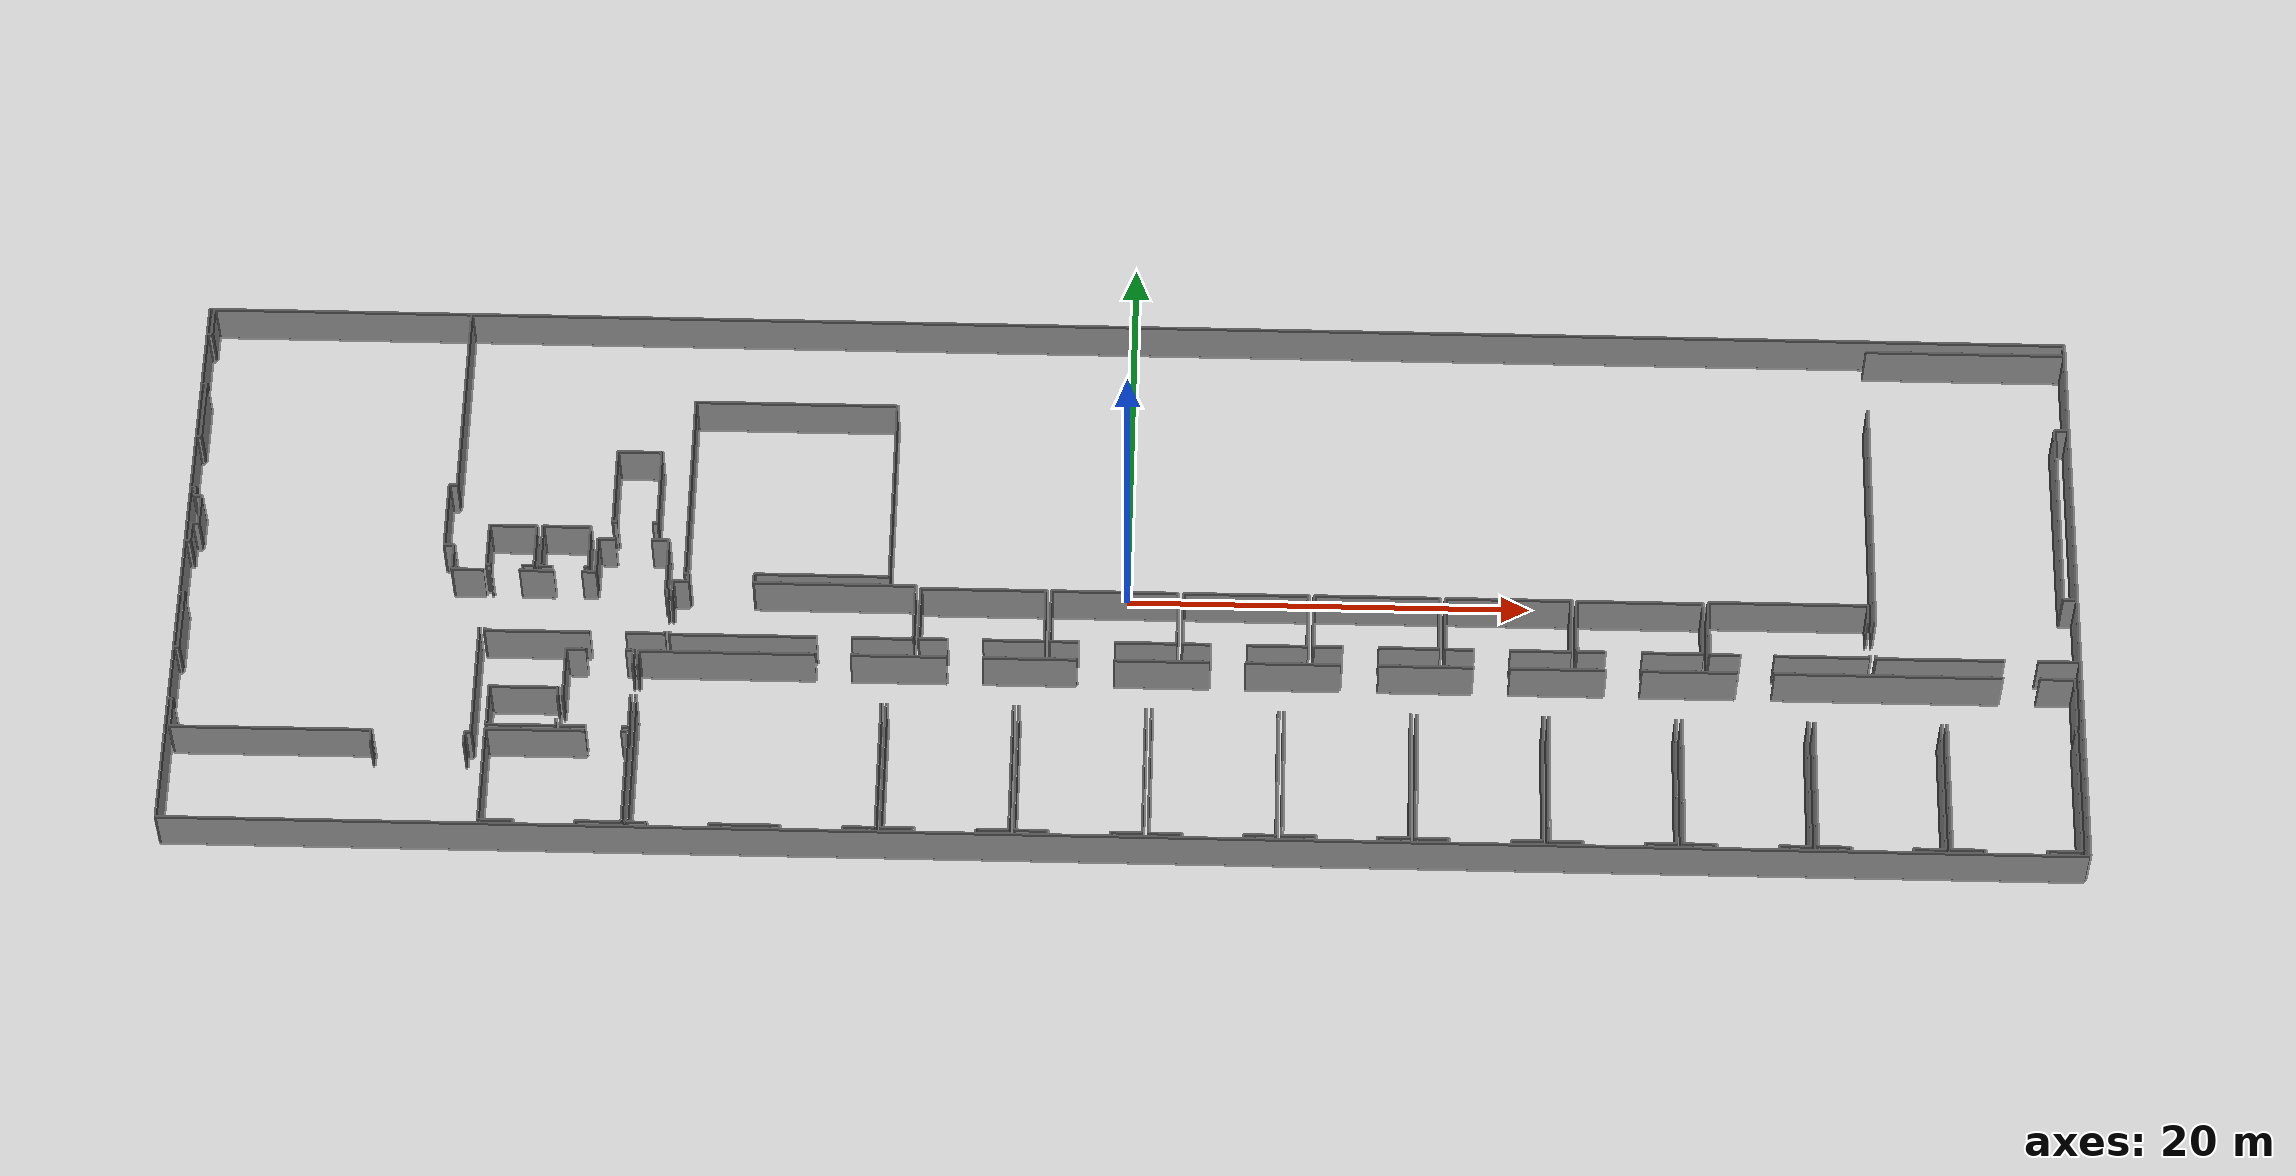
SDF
<sdf version="1.6">
  <world name="default">
    <light name="sun" type="directional">
      <cast_shadows>1</cast_shadows>
      <pose frame="">0 0 10 0 -0 0</pose>
      <diffuse>0.8 0.8 0.8 1</diffuse>
      <specular>0.1 0.1 0.1 1</specular>
      <attenuation>
        <range>1000</range>
        <constant>0.9</constant>
        <linear>0.01</linear>
        <quadratic>0.001</quadratic>
      </attenuation>
      <direction>-0.5 0.5 -1</direction>
    </light>
    <model name="ground_plane">
      <static>1</static>
      <link name="link">
        <collision name="collision">
          <geometry>
            <plane>
              <normal>0 0 1</normal>
              <size>100 100</size>
            </plane>
          </geometry>
          <surface>
            <friction>
              <ode>
                <mu>100</mu>
                <mu2>50</mu2>
              </ode>
              <torsional>
                <ode />
              </torsional>
            </friction>
            <contact>
              <ode />
            </contact>
            <bounce />
          </surface>
          <max_contacts>10</max_contacts>
        </collision>
        <visual name="visual">
          <cast_shadows>0</cast_shadows>
          <geometry>
            <plane>
              <normal>0 0 1</normal>
              <size>100 100</size>
            </plane>
          </geometry>
          <material>
            <script>
              <uri>file://media/materials/scripts/gazebo.material</uri>
              <name>Gazebo/Grey</name>
            </script>
          </material>
        </visual>
        <self_collide>0</self_collide>
        <kinematic>0</kinematic>
        <gravity>1</gravity>
      </link>
    </model>
    <gravity>0 0 -9.8</gravity>
    <magnetic_field>6e-06 2.3e-05 -4.2e-05</magnetic_field>
    <atmosphere type="adiabatic" />
    <physics default="0" name="default_physics" type="ode">
      <max_step_size>0.001</max_step_size>
      <real_time_factor>1</real_time_factor>
      <real_time_update_rate>1000</real_time_update_rate>
    </physics>
    <scene>
      <ambient>0.4 0.4 0.4 1</ambient>
      <background>0.7 0.7 0.7 1</background>
      <shadows>1</shadows>
    </scene>
    <spherical_coordinates>
      <surface_model>EARTH_WGS84</surface_model>
      <latitude_deg>0</latitude_deg>
      <longitude_deg>0</longitude_deg>
      <elevation>0</elevation>
      <heading_deg>0</heading_deg>
    </spherical_coordinates>
  <model name="50045231">
		<static>1</static>
		<link name="Wall_0">
			<collision name="Wall_0_Collision">
				<geometry>
					<box>
						<size>1.54801707894 0.1 2.5</size>
					</box>
				</geometry>
				<pose frame="">0.774008539471 0 1.25 0 0 0</pose>
			</collision>
			<visual name="Wall_0_Visual">
				<pose frame="">0.774008539471 0 1.25 0 0 0</pose>
				<geometry>
					<box>
						<size>1.54801707894 0.1 2.5</size>
					</box>
				</geometry>
				<material>
					<script>
						<uri>file://media/materials/scripts/gazebo.material</uri>
						<name>Gazebo/Grey</name>
					</script>
					<ambient>1 1 1 1</ambient>
				</material>
			</visual>
			<pose frame="">0.215707297885 -24.7173917181 0 0 0 1.57079632679</pose>
		</link>
		<link name="Wall_1">
			<collision name="Wall_1_Collision">
				<geometry>
					<box>
						<size>0.215707297885 0.1 2.5</size>
					</box>
				</geometry>
				<pose frame="">0.107853648943 0 1.25 0 0 0</pose>
			</collision>
			<visual name="Wall_1_Visual">
				<pose frame="">0.107853648943 0 1.25 0 0 0</pose>
				<geometry>
					<box>
						<size>0.215707297885 0.1 2.5</size>
					</box>
				</geometry>
				<material>
					<script>
						<uri>file://media/materials/scripts/gazebo.material</uri>
						<name>Gazebo/Grey</name>
					</script>
					<ambient>1 1 1 1</ambient>
				</material>
			</visual>
			<pose frame="">0.215707297885 -23.1693746392 0 0 0 3.14159265359</pose>
		</link>
		<link name="Wall_2">
			<collision name="Wall_2_Collision">
				<geometry>
					<box>
						<size>0.233090768362 0.1 2.5</size>
					</box>
				</geometry>
				<pose frame="">0.116545384181 0 1.25 0 0 0</pose>
			</collision>
			<visual name="Wall_2_Visual">
				<pose frame="">0.116545384181 0 1.25 0 0 0</pose>
				<geometry>
					<box>
						<size>0.233090768362 0.1 2.5</size>
					</box>
				</geometry>
				<material>
					<script>
						<uri>file://media/materials/scripts/gazebo.material</uri>
						<name>Gazebo/Grey</name>
					</script>
					<ambient>1 1 1 1</ambient>
				</material>
			</visual>
			<pose frame="">0.0 -20.1388139905 0 0 0 0.0</pose>
		</link>
		<link name="Wall_3">
			<collision name="Wall_3_Collision">
				<geometry>
					<box>
						<size>3.15440201496 0.1 2.5</size>
					</box>
				</geometry>
				<pose frame="">1.57720100748 0 1.25 0 0 0</pose>
			</collision>
			<visual name="Wall_3_Visual">
				<pose frame="">1.57720100748 0 1.25 0 0 0</pose>
				<geometry>
					<box>
						<size>3.15440201496 0.1 2.5</size>
					</box>
				</geometry>
				<material>
					<script>
						<uri>file://media/materials/scripts/gazebo.material</uri>
						<name>Gazebo/Grey</name>
					</script>
					<ambient>1 1 1 1</ambient>
				</material>
			</visual>
			<pose frame="">0.233090768362 -20.1388139905 0 0 0 1.57079632679</pose>
		</link>
		<link name="Wall_4">
			<collision name="Wall_4_Collision">
				<geometry>
					<box>
						<size>0.206063912803 0.1 2.5</size>
					</box>
				</geometry>
				<pose frame="">0.103031956402 0 1.25 0 0 0</pose>
			</collision>
			<visual name="Wall_4_Visual">
				<pose frame="">0.103031956402 0 1.25 0 0 0</pose>
				<geometry>
					<box>
						<size>0.206063912803 0.1 2.5</size>
					</box>
				</geometry>
				<material>
					<script>
						<uri>file://media/materials/scripts/gazebo.material</uri>
						<name>Gazebo/Grey</name>
					</script>
					<ambient>1 1 1 1</ambient>
				</material>
			</visual>
			<pose frame="">0.233090768362 -16.9844119756 0 0 0 3.14159265359</pose>
		</link>
		<link name="Wall_5">
			<collision name="Wall_5_Collision">
				<geometry>
					<box>
						<size>0.215834184531 0.1 2.5</size>
					</box>
				</geometry>
				<pose frame="">0.107917092266 0 1.25 0 0 0</pose>
			</collision>
			<visual name="Wall_5_Visual">
				<pose frame="">0.107917092266 0 1.25 0 0 0</pose>
				<geometry>
					<box>
						<size>0.215834184531 0.1 2.5</size>
					</box>
				</geometry>
				<material>
					<script>
						<uri>file://media/materials/scripts/gazebo.material</uri>
						<name>Gazebo/Grey</name>
					</script>
					<ambient>1 1 1 1</ambient>
				</material>
			</visual>
			<pose frame="">0.0270268555586 -13.9289815443 0 0 0 0.0</pose>
		</link>
		<link name="Wall_6">
			<collision name="Wall_6_Collision">
				<geometry>
					<box>
						<size>1.02803560439 0.1 2.5</size>
					</box>
				</geometry>
				<pose frame="">0.514017802196 0 1.25 0 0 0</pose>
			</collision>
			<visual name="Wall_6_Visual">
				<pose frame="">0.514017802196 0 1.25 0 0 0</pose>
				<geometry>
					<box>
						<size>1.02803560439 0.1 2.5</size>
					</box>
				</geometry>
				<material>
					<script>
						<uri>file://media/materials/scripts/gazebo.material</uri>
						<name>Gazebo/Grey</name>
					</script>
					<ambient>1 1 1 1</ambient>
				</material>
			</visual>
			<pose frame="">0.24286104009 -13.9289815443 0 0 0 1.57079632679</pose>
		</link>
		<link name="Wall_7">
			<collision name="Wall_7_Collision">
				<geometry>
					<box>
						<size>0.333711878493 0.1 2.5</size>
					</box>
				</geometry>
				<pose frame="">0.166855939247 0 1.25 0 0 0</pose>
			</collision>
			<visual name="Wall_7_Visual">
				<pose frame="">0.166855939247 0 1.25 0 0 0</pose>
				<geometry>
					<box>
						<size>0.333711878493 0.1 2.5</size>
					</box>
				</geometry>
				<material>
					<script>
						<uri>file://media/materials/scripts/gazebo.material</uri>
						<name>Gazebo/Grey</name>
					</script>
					<ambient>1 1 1 1</ambient>
				</material>
			</visual>
			<pose frame="">0.24286104009 -12.9009459399 0 0 0 0.0</pose>
		</link>
		<link name="Wall_8">
			<collision name="Wall_8_Collision">
				<geometry>
					<box>
						<size>1.6478768692 0.1 2.5</size>
					</box>
				</geometry>
				<pose frame="">0.823938434599 0 1.25 0 0 0</pose>
			</collision>
			<visual name="Wall_8_Visual">
				<pose frame="">0.823938434599 0 1.25 0 0 0</pose>
				<geometry>
					<box>
						<size>1.6478768692 0.1 2.5</size>
					</box>
				</geometry>
				<material>
					<script>
						<uri>file://media/materials/scripts/gazebo.material</uri>
						<name>Gazebo/Grey</name>
					</script>
					<ambient>1 1 1 1</ambient>
				</material>
			</visual>
			<pose frame="">0.576572918583 -12.9009459399 0 0 0 1.57079632679</pose>
		</link>
		<link name="Wall_9">
			<collision name="Wall_9_Collision">
				<geometry>
					<box>
						<size>0.324576039995 0.1 2.5</size>
					</box>
				</geometry>
				<pose frame="">0.162288019997 0 1.25 0 0 0</pose>
			</collision>
			<visual name="Wall_9_Visual">
				<pose frame="">0.162288019997 0 1.25 0 0 0</pose>
				<geometry>
					<box>
						<size>0.324576039995 0.1 2.5</size>
					</box>
				</geometry>
				<material>
					<script>
						<uri>file://media/materials/scripts/gazebo.material</uri>
						<name>Gazebo/Grey</name>
					</script>
					<ambient>1 1 1 1</ambient>
				</material>
			</visual>
			<pose frame="">0.576572918583 -11.2530690707 0 0 0 3.14159265359</pose>
		</link>
		<link name="Wall_10">
			<collision name="Wall_10_Collision">
				<geometry>
					<box>
						<size>0.47874331466 0.1 2.5</size>
					</box>
				</geometry>
				<pose frame="">0.23937165733 0 1.25 0 0 0</pose>
			</collision>
			<visual name="Wall_10_Visual">
				<pose frame="">0.23937165733 0 1.25 0 0 0</pose>
				<geometry>
					<box>
						<size>0.47874331466 0.1 2.5</size>
					</box>
				</geometry>
				<material>
					<script>
						<uri>file://media/materials/scripts/gazebo.material</uri>
						<name>Gazebo/Grey</name>
					</script>
					<ambient>1 1 1 1</ambient>
				</material>
			</visual>
			<pose frame="">0.251996878589 -11.2530690707 0 0 0 1.57079632679</pose>
		</link>
		<link name="Wall_11">
			<collision name="Wall_11_Collision">
				<geometry>
					<box>
						<size>0.239435100653 0.1 2.5</size>
					</box>
				</geometry>
				<pose frame="">0.119717550326 0 1.25 0 0 0</pose>
			</collision>
			<visual name="Wall_11_Visual">
				<pose frame="">0.119717550326 0 1.25 0 0 0</pose>
				<geometry>
					<box>
						<size>0.239435100653 0.1 2.5</size>
					</box>
				</geometry>
				<material>
					<script>
						<uri>file://media/materials/scripts/gazebo.material</uri>
						<name>Gazebo/Grey</name>
					</script>
					<ambient>1 1 1 1</ambient>
				</material>
			</visual>
			<pose frame="">0.251996878589 -10.7743257561 0 0 0 3.14159265359</pose>
		</link>
		<link name="Wall_12">
			<collision name="Wall_12_Collision">
				<geometry>
					<box>
						<size>0.221670970239 0.1 2.5</size>
					</box>
				</geometry>
				<pose frame="">0.110835485119 0 1.25 0 0 0</pose>
			</collision>
			<visual name="Wall_12_Visual">
				<pose frame="">0.110835485119 0 1.25 0 0 0</pose>
				<geometry>
					<box>
						<size>0.221670970239 0.1 2.5</size>
					</box>
				</geometry>
				<material>
					<script>
						<uri>file://media/materials/scripts/gazebo.material</uri>
						<name>Gazebo/Grey</name>
					</script>
					<ambient>1 1 1 1</ambient>
				</material>
			</visual>
			<pose frame="">0.0125617779357 -7.7358981354 0 0 0 0.0</pose>
		</link>
		<link name="Wall_13">
			<collision name="Wall_13_Collision">
				<geometry>
					<box>
						<size>3.17077039227 0.1 2.5</size>
					</box>
				</geometry>
				<pose frame="">1.58538519614 0 1.25 0 0 0</pose>
			</collision>
			<visual name="Wall_13_Visual">
				<pose frame="">1.58538519614 0 1.25 0 0 0</pose>
				<geometry>
					<box>
						<size>3.17077039227 0.1 2.5</size>
					</box>
				</geometry>
				<material>
					<script>
						<uri>file://media/materials/scripts/gazebo.material</uri>
						<name>Gazebo/Grey</name>
					</script>
					<ambient>1 1 1 1</ambient>
				</material>
			</visual>
			<pose frame="">0.234232748174 -7.7358981354 0 0 0 1.57079632679</pose>
		</link>
		<link name="Wall_14">
			<collision name="Wall_14_Collision">
				<geometry>
					<box>
						<size>0.229918602217 0.1 2.5</size>
					</box>
				</geometry>
				<pose frame="">0.114959301108 0 1.25 0 0 0</pose>
			</collision>
			<visual name="Wall_14_Visual">
				<pose frame="">0.114959301108 0 1.25 0 0 0</pose>
				<geometry>
					<box>
						<size>0.229918602217 0.1 2.5</size>
					</box>
				</geometry>
				<material>
					<script>
						<uri>file://media/materials/scripts/gazebo.material</uri>
						<name>Gazebo/Grey</name>
					</script>
					<ambient>1 1 1 1</ambient>
				</material>
			</visual>
			<pose frame="">0.234232748174 -4.56512774313 0 0 0 3.14159265359</pose>
		</link>
		<link name="Wall_15">
			<collision name="Wall_15_Collision">
				<geometry>
					<box>
						<size>0.234994068049 0.1 2.5</size>
					</box>
				</geometry>
				<pose frame="">0.117497034025 0 1.25 0 0 0</pose>
			</collision>
			<visual name="Wall_15_Visual">
				<pose frame="">0.117497034025 0 1.25 0 0 0</pose>
				<geometry>
					<box>
						<size>0.234994068049 0.1 2.5</size>
					</box>
				</geometry>
				<material>
					<script>
						<uri>file://media/materials/scripts/gazebo.material</uri>
						<name>Gazebo/Grey</name>
					</script>
					<ambient>1 1 1 1</ambient>
				</material>
			</visual>
			<pose frame="">0.00431414595771 -1.54827085223 0 0 0 0.0</pose>
		</link>
		<link name="Wall_16">
			<collision name="Wall_16_Collision">
				<geometry>
					<box>
						<size>1.54827085223 0.1 2.5</size>
					</box>
				</geometry>
				<pose frame="">0.774135426117 0 1.25 0 0 0</pose>
			</collision>
			<visual name="Wall_16_Visual">
				<pose frame="">0.774135426117 0 1.25 0 0 0</pose>
				<geometry>
					<box>
						<size>1.54827085223 0.1 2.5</size>
					</box>
				</geometry>
				<material>
					<script>
						<uri>file://media/materials/scripts/gazebo.material</uri>
						<name>Gazebo/Grey</name>
					</script>
					<ambient>1 1 1 1</ambient>
				</material>
			</visual>
			<pose frame="">0.239308214007 -1.54827085223 0 0 0 1.57079632679</pose>
		</link>
		<link name="Wall_17">
			<collision name="Wall_17_Collision">
				<geometry>
					<box>
						<size>13.071100932 0.1 2.5</size>
					</box>
				</geometry>
				<pose frame="">6.53555046599 0 1.25 0 0 0</pose>
			</collision>
			<visual name="Wall_17_Visual">
				<pose frame="">6.53555046599 0 1.25 0 0 0</pose>
				<geometry>
					<box>
						<size>13.071100932 0.1 2.5</size>
					</box>
				</geometry>
				<material>
					<script>
						<uri>file://media/materials/scripts/gazebo.material</uri>
						<name>Gazebo/Grey</name>
					</script>
					<ambient>1 1 1 1</ambient>
				</material>
			</visual>
			<pose frame="">0.239308214007 -0.0 0 0 0 0.0</pose>
		</link>
		<link name="Wall_18">
			<collision name="Wall_18_Collision">
				<geometry>
					<box>
						<size>10.3030687535 0.1 2.5</size>
					</box>
				</geometry>
				<pose frame="">5.15153437676 0 1.25 0 0 0</pose>
			</collision>
			<visual name="Wall_18_Visual">
				<pose frame="">5.15153437676 0 1.25 0 0 0</pose>
				<geometry>
					<box>
						<size>10.3030687535 0.1 2.5</size>
					</box>
				</geometry>
				<material>
					<script>
						<uri>file://media/materials/scripts/gazebo.material</uri>
						<name>Gazebo/Grey</name>
					</script>
					<ambient>1 1 1 1</ambient>
				</material>
			</visual>
			<pose frame="">13.310409146 -0.0 0 0 0 -1.57079632679</pose>
		</link>
		<link name="Wall_19">
			<collision name="Wall_19_Collision">
				<geometry>
					<box>
						<size>0.393348602026 0.1 2.5</size>
					</box>
				</geometry>
				<pose frame="">0.196674301013 0 1.25 0 0 0</pose>
			</collision>
			<visual name="Wall_19_Visual">
				<pose frame="">0.196674301013 0 1.25 0 0 0</pose>
				<geometry>
					<box>
						<size>0.393348602026 0.1 2.5</size>
					</box>
				</geometry>
				<material>
					<script>
						<uri>file://media/materials/scripts/gazebo.material</uri>
						<name>Gazebo/Grey</name>
					</script>
					<ambient>1 1 1 1</ambient>
				</material>
			</visual>
			<pose frame="">13.310409146 -10.3030687535 0 0 0 3.14159265359</pose>
		</link>
		<link name="Wall_20">
			<collision name="Wall_20_Collision">
				<geometry>
					<box>
						<size>3.56183503467 0.1 2.5</size>
					</box>
				</geometry>
				<pose frame="">1.78091751734 0 1.25 0 0 0</pose>
			</collision>
			<visual name="Wall_20_Visual">
				<pose frame="">1.78091751734 0 1.25 0 0 0</pose>
				<geometry>
					<box>
						<size>3.56183503467 0.1 2.5</size>
					</box>
				</geometry>
				<material>
					<script>
						<uri>file://media/materials/scripts/gazebo.material</uri>
						<name>Gazebo/Grey</name>
					</script>
					<ambient>1 1 1 1</ambient>
				</material>
			</visual>
			<pose frame="">12.917060544 -10.3030687535 0 0 0 -1.57079632679</pose>
		</link>
		<link name="Wall_21">
			<collision name="Wall_21_Collision">
				<geometry>
					<box>
						<size>0.4896555662 0.1 2.5</size>
					</box>
				</geometry>
				<pose frame="">0.2448277831 0 1.25 0 0 0</pose>
			</collision>
			<visual name="Wall_21_Visual">
				<pose frame="">0.2448277831 0 1.25 0 0 0</pose>
				<geometry>
					<box>
						<size>0.4896555662 0.1 2.5</size>
					</box>
				</geometry>
				<material>
					<script>
						<uri>file://media/materials/scripts/gazebo.material</uri>
						<name>Gazebo/Grey</name>
					</script>
					<ambient>1 1 1 1</ambient>
				</material>
			</visual>
			<pose frame="">12.917060544 -13.8649037882 0 0 0 0.0</pose>
		</link>
		<link name="Wall_22">
			<collision name="Wall_22_Collision">
				<geometry>
					<box>
						<size>1.41821204027 0.1 2.5</size>
					</box>
				</geometry>
				<pose frame="">0.709106020137 0 1.25 0 0 0</pose>
			</collision>
			<visual name="Wall_22_Visual">
				<pose frame="">0.709106020137 0 1.25 0 0 0</pose>
				<geometry>
					<box>
						<size>1.41821204027 0.1 2.5</size>
					</box>
				</geometry>
				<material>
					<script>
						<uri>file://media/materials/scripts/gazebo.material</uri>
						<name>Gazebo/Grey</name>
					</script>
					<ambient>1 1 1 1</ambient>
				</material>
			</visual>
			<pose frame="">13.4067161102 -13.8649037882 0 0 0 -1.57079632679</pose>
		</link>
		<link name="Wall_23">
			<collision name="Wall_23_Collision">
				<geometry>
					<box>
						<size>1.59344249814 0.1 2.5</size>
					</box>
				</geometry>
				<pose frame="">0.796721249072 0 1.25 0 0 0</pose>
			</collision>
			<visual name="Wall_23_Visual">
				<pose frame="">0.796721249072 0 1.25 0 0 0</pose>
				<geometry>
					<box>
						<size>1.59344249814 0.1 2.5</size>
					</box>
				</geometry>
				<material>
					<script>
						<uri>file://media/materials/scripts/gazebo.material</uri>
						<name>Gazebo/Grey</name>
					</script>
					<ambient>1 1 1 1</ambient>
				</material>
			</visual>
			<pose frame="">13.4067161102 -15.2831158285 0 0 0 0.0</pose>
		</link>
		<link name="Wall_24">
			<collision name="Wall_24_Collision">
				<geometry>
					<box>
						<size>6.01163550542 0.1 2.5</size>
					</box>
				</geometry>
				<pose frame="">3.00581775271 0 1.25 0 0 0</pose>
			</collision>
			<visual name="Wall_24_Visual">
				<pose frame="">3.00581775271 0 1.25 0 0 0</pose>
				<geometry>
					<box>
						<size>6.01163550542 0.1 2.5</size>
					</box>
				</geometry>
				<material>
					<script>
						<uri>file://media/materials/scripts/gazebo.material</uri>
						<name>Gazebo/Grey</name>
					</script>
					<ambient>1 1 1 1</ambient>
				</material>
			</visual>
			<pose frame="">15.0001586083 -18.6902760419 0 0 0 -1.57079632679</pose>
		</link>
		<link name="Wall_25">
			<collision name="Wall_25_Collision">
				<geometry>
					<box>
						<size>0.299452484123 0.1 2.5</size>
					</box>
				</geometry>
				<pose frame="">0.149726242062 0 1.25 0 0 0</pose>
			</collision>
			<visual name="Wall_25_Visual">
				<pose frame="">0.149726242062 0 1.25 0 0 0</pose>
				<geometry>
					<box>
						<size>0.299452484123 0.1 2.5</size>
					</box>
				</geometry>
				<material>
					<script>
						<uri>file://media/materials/scripts/gazebo.material</uri>
						<name>Gazebo/Grey</name>
					</script>
					<ambient>1 1 1 1</ambient>
				</material>
			</visual>
			<pose frame="">15.0001586083 -24.7019115473 0 0 0 3.14159265359</pose>
		</link>
		<link name="Wall_26">
			<collision name="Wall_26_Collision">
				<geometry>
					<box>
						<size>0.640016241491 0.1 2.5</size>
					</box>
				</geometry>
				<pose frame="">0.320008120745 0 1.25 0 0 0</pose>
			</collision>
			<visual name="Wall_26_Visual">
				<pose frame="">0.320008120745 0 1.25 0 0 0</pose>
				<geometry>
					<box>
						<size>0.640016241491 0.1 2.5</size>
					</box>
				</geometry>
				<material>
					<script>
						<uri>file://media/materials/scripts/gazebo.material</uri>
						<name>Gazebo/Grey</name>
					</script>
					<ambient>1 1 1 1</ambient>
				</material>
			</visual>
			<pose frame="">14.7007061242 -24.7019115473 0 0 0 -1.57079632679</pose>
		</link>
		<link name="Wall_27">
			<collision name="Wall_27_Collision">
				<geometry>
					<box>
						<size>0.651055379677 0.1 2.5</size>
					</box>
				</geometry>
				<pose frame="">0.325527689838 0 1.25 0 0 0</pose>
			</collision>
			<visual name="Wall_27_Visual">
				<pose frame="">0.325527689838 0 1.25 0 0 0</pose>
				<geometry>
					<box>
						<size>0.651055379677 0.1 2.5</size>
					</box>
				</geometry>
				<material>
					<script>
						<uri>file://media/materials/scripts/gazebo.material</uri>
						<name>Gazebo/Grey</name>
					</script>
					<ambient>1 1 1 1</ambient>
				</material>
			</visual>
			<pose frame="">10.1217477367 -25.3419277888 0 0 0 1.57079632679</pose>
		</link>
		<link name="Wall_28">
			<collision name="Wall_28_Collision">
				<geometry>
					<box>
						<size>9.90607593593 0.1 2.5</size>
					</box>
				</geometry>
				<pose frame="">4.95303796796 0 1.25 0 0 0</pose>
			</collision>
			<visual name="Wall_28_Visual">
				<pose frame="">4.95303796796 0 1.25 0 0 0</pose>
				<geometry>
					<box>
						<size>9.90607593593 0.1 2.5</size>
					</box>
				</geometry>
				<material>
					<script>
						<uri>file://media/materials/scripts/gazebo.material</uri>
						<name>Gazebo/Grey</name>
					</script>
					<ambient>1 1 1 1</ambient>
				</material>
			</visual>
			<pose frame="">10.1217477367 -24.6908724091 0 0 0 -3.13891557532</pose>
		</link>
		<link name="Wall_29">
			<collision name="Wall_29_Collision">
				<geometry>
					<box>
						<size>0.125110232774 0.1 2.5</size>
					</box>
				</geometry>
				<pose frame="">0.0625551163868 0 1.25 0 0 0</pose>
			</collision>
			<visual name="Wall_29_Visual">
				<pose frame="">0.0625551163868 0 1.25 0 0 0</pose>
				<geometry>
					<box>
						<size>0.125110232774 0.1 2.5</size>
					</box>
				</geometry>
				<material>
					<script>
						<uri>file://media/materials/scripts/gazebo.material</uri>
						<name>Gazebo/Grey</name>
					</script>
					<ambient>1 1 1 1</ambient>
				</material>
			</visual>
			<pose frame="">15.2588804791 -18.8205886271 0 0 0 1.57079632679</pose>
		</link>
		<link name="Wall_30">
			<collision name="Wall_30_Collision">
				<geometry>
					<box>
						<size>0.125110232774 0.1 2.5</size>
					</box>
				</geometry>
				<pose frame="">0.0625551163868 0 1.25 0 0 0</pose>
			</collision>
			<visual name="Wall_30_Visual">
				<pose frame="">0.0625551163868 0 1.25 0 0 0</pose>
				<geometry>
					<box>
						<size>0.125110232774 0.1 2.5</size>
					</box>
				</geometry>
				<material>
					<script>
						<uri>file://media/materials/scripts/gazebo.material</uri>
						<name>Gazebo/Grey</name>
					</script>
					<ambient>1 1 1 1</ambient>
				</material>
			</visual>
			<pose frame="">15.2588804791 -15.2748681965 0 0 0 0.0</pose>
		</link>
		<link name="Wall_31">
			<collision name="Wall_31_Collision">
				<geometry>
					<box>
						<size>1.72667347625 0.1 2.5</size>
					</box>
				</geometry>
				<pose frame="">0.863336738125 0 1.25 0 0 0</pose>
			</collision>
			<visual name="Wall_31_Visual">
				<pose frame="">0.863336738125 0 1.25 0 0 0</pose>
				<geometry>
					<box>
						<size>1.72667347625 0.1 2.5</size>
					</box>
				</geometry>
				<material>
					<script>
						<uri>file://media/materials/scripts/gazebo.material</uri>
						<name>Gazebo/Grey</name>
					</script>
					<ambient>1 1 1 1</ambient>
				</material>
			</visual>
			<pose frame="">16.7492910209 -15.2748681965 0 0 0 0.0</pose>
		</link>
		<link name="Wall_32">
			<collision name="Wall_32_Collision">
				<geometry>
					<box>
						<size>0.70916946346 0.1 2.5</size>
					</box>
				</geometry>
				<pose frame="">0.35458473173 0 1.25 0 0 0</pose>
			</collision>
			<visual name="Wall_32_Visual">
				<pose frame="">0.35458473173 0 1.25 0 0 0</pose>
				<geometry>
					<box>
						<size>0.70916946346 0.1 2.5</size>
					</box>
				</geometry>
				<material>
					<script>
						<uri>file://media/materials/scripts/gazebo.material</uri>
						<name>Gazebo/Grey</name>
					</script>
					<ambient>1 1 1 1</ambient>
				</material>
			</visual>
			<pose frame="">19.8474822517 -15.2748681965 0 0 0 0.0</pose>
		</link>
		<link name="Wall_33">
			<collision name="Wall_33_Collision">
				<geometry>
					<box>
						<size>1.95227793251 0.1 2.5</size>
					</box>
				</geometry>
				<pose frame="">0.976138966254 0 1.25 0 0 0</pose>
			</collision>
			<visual name="Wall_33_Visual">
				<pose frame="">0.976138966254 0 1.25 0 0 0</pose>
				<geometry>
					<box>
						<size>1.95227793251 0.1 2.5</size>
					</box>
				</geometry>
				<material>
					<script>
						<uri>file://media/materials/scripts/gazebo.material</uri>
						<name>Gazebo/Grey</name>
					</script>
					<ambient>1 1 1 1</ambient>
				</material>
			</visual>
			<pose frame="">20.5566517152 -15.2748681965 0 0 0 1.57079632679</pose>
		</link>
		<link name="Wall_34">
			<collision name="Wall_34_Collision">
				<geometry>
					<box>
						<size>0.859276365459 0.1 2.5</size>
					</box>
				</geometry>
				<pose frame="">0.429638182729 0 1.25 0 0 0</pose>
			</collision>
			<visual name="Wall_34_Visual">
				<pose frame="">0.429638182729 0 1.25 0 0 0</pose>
				<geometry>
					<box>
						<size>0.859276365459 0.1 2.5</size>
					</box>
				</geometry>
				<material>
					<script>
						<uri>file://media/materials/scripts/gazebo.material</uri>
						<name>Gazebo/Grey</name>
					</script>
					<ambient>1 1 1 1</ambient>
				</material>
			</visual>
			<pose frame="">20.5566517152 -13.322590264 0 0 0 0.0</pose>
		</link>
		<link name="Wall_35">
			<collision name="Wall_35_Collision">
				<geometry>
					<box>
						<size>0.870569276936 0.1 2.5</size>
					</box>
				</geometry>
				<pose frame="">0.435284638468 0 1.25 0 0 0</pose>
			</collision>
			<visual name="Wall_35_Visual">
				<pose frame="">0.435284638468 0 1.25 0 0 0</pose>
				<geometry>
					<box>
						<size>0.870569276936 0.1 2.5</size>
					</box>
				</geometry>
				<material>
					<script>
						<uri>file://media/materials/scripts/gazebo.material</uri>
						<name>Gazebo/Grey</name>
					</script>
					<ambient>1 1 1 1</ambient>
				</material>
			</visual>
			<pose frame="">23.2134043053 -13.322590264 0 0 0 0.0</pose>
		</link>
		<link name="Wall_36">
			<collision name="Wall_36_Collision">
				<geometry>
					<box>
						<size>2.92372209287 0.1 2.5</size>
					</box>
				</geometry>
				<pose frame="">1.46186104643 0 1.25 0 0 0</pose>
			</collision>
			<visual name="Wall_36_Visual">
				<pose frame="">1.46186104643 0 1.25 0 0 0</pose>
				<geometry>
					<box>
						<size>2.92372209287 0.1 2.5</size>
					</box>
				</geometry>
				<material>
					<script>
						<uri>file://media/materials/scripts/gazebo.material</uri>
						<name>Gazebo/Grey</name>
					</script>
					<ambient>1 1 1 1</ambient>
				</material>
			</visual>
			<pose frame="">24.0839735822 -13.322590264 0 0 0 -1.57079632679</pose>
		</link>
		<link name="Wall_37">
			<collision name="Wall_37_Collision">
				<geometry>
					<box>
						<size>0.121938066628 0.1 2.5</size>
					</box>
				</geometry>
				<pose frame="">0.0609690333141 0 1.25 0 0 0</pose>
			</collision>
			<visual name="Wall_37_Visual">
				<pose frame="">0.0609690333141 0 1.25 0 0 0</pose>
				<geometry>
					<box>
						<size>0.121938066628 0.1 2.5</size>
					</box>
				</geometry>
				<material>
					<script>
						<uri>file://media/materials/scripts/gazebo.material</uri>
						<name>Gazebo/Grey</name>
					</script>
					<ambient>1 1 1 1</ambient>
				</material>
			</visual>
			<pose frame="">24.0839735822 -16.2463123569 0 0 0 0.0</pose>
		</link>
		<link name="Wall_38">
			<collision name="Wall_38_Collision">
				<geometry>
					<box>
						<size>0.450955139226 0.1 2.5</size>
					</box>
				</geometry>
				<pose frame="">0.225477569613 0 1.25 0 0 0</pose>
			</collision>
			<visual name="Wall_38_Visual">
				<pose frame="">0.225477569613 0 1.25 0 0 0</pose>
				<geometry>
					<box>
						<size>0.450955139226 0.1 2.5</size>
					</box>
				</geometry>
				<material>
					<script>
						<uri>file://media/materials/scripts/gazebo.material</uri>
						<name>Gazebo/Grey</name>
					</script>
					<ambient>1 1 1 1</ambient>
				</material>
			</visual>
			<pose frame="">24.2059116488 -16.2463123569 0 0 0 -1.57079632679</pose>
		</link>
		<link name="Wall_39">
			<collision name="Wall_39_Collision">
				<geometry>
					<box>
						<size>0.115086187754 0.1 2.5</size>
					</box>
				</geometry>
				<pose frame="">0.0575430938771 0 1.25 0 0 0</pose>
			</collision>
			<visual name="Wall_39_Visual">
				<pose frame="">0.0575430938771 0 1.25 0 0 0</pose>
				<geometry>
					<box>
						<size>0.115086187754 0.1 2.5</size>
					</box>
				</geometry>
				<material>
					<script>
						<uri>file://media/materials/scripts/gazebo.material</uri>
						<name>Gazebo/Grey</name>
					</script>
					<ambient>1 1 1 1</ambient>
				</material>
			</visual>
			<pose frame="">24.2059116488 -18.6929406615 0 0 0 -1.57079632679</pose>
		</link>
		<link name="Wall_40">
			<collision name="Wall_40_Collision">
				<geometry>
					<box>
						<size>1.95735339834 0.1 2.5</size>
					</box>
				</geometry>
				<pose frame="">0.978676699171 0 1.25 0 0 0</pose>
			</collision>
			<visual name="Wall_40_Visual">
				<pose frame="">0.978676699171 0 1.25 0 0 0</pose>
				<geometry>
					<box>
						<size>1.95735339834 0.1 2.5</size>
					</box>
				</geometry>
				<material>
					<script>
						<uri>file://media/materials/scripts/gazebo.material</uri>
						<name>Gazebo/Grey</name>
					</script>
					<ambient>1 1 1 1</ambient>
				</material>
			</visual>
			<pose frame="">24.2059116488 -18.8080268492 0 0 0 3.14159265359</pose>
		</link>
		<link name="Wall_41">
			<collision name="Wall_41_Collision">
				<geometry>
					<box>
						<size>5.2339623277 0.1 2.5</size>
					</box>
				</geometry>
				<pose frame="">2.61698116385 0 1.25 0 0 0</pose>
			</collision>
			<visual name="Wall_41_Visual">
				<pose frame="">2.61698116385 0 1.25 0 0 0</pose>
				<geometry>
					<box>
						<size>5.2339623277 0.1 2.5</size>
					</box>
				</geometry>
				<material>
					<script>
						<uri>file://media/materials/scripts/gazebo.material</uri>
						<name>Gazebo/Grey</name>
					</script>
					<ambient>1 1 1 1</ambient>
				</material>
			</visual>
			<pose frame="">20.4928277323 -18.8080268492 0 0 0 -3.13919260001</pose>
		</link>
		<link name="Wall_42">
			<collision name="Wall_42_Collision">
				<geometry>
					<box>
						<size>0.200227127096 0.1 2.5</size>
					</box>
				</geometry>
				<pose frame="">0.100113563548 0 1.25 0 0 0</pose>
			</collision>
			<visual name="Wall_42_Visual">
				<pose frame="">0.100113563548 0 1.25 0 0 0</pose>
				<geometry>
					<box>
						<size>0.200227127096 0.1 2.5</size>
					</box>
				</geometry>
				<material>
					<script>
						<uri>file://media/materials/scripts/gazebo.material</uri>
						<name>Gazebo/Grey</name>
					</script>
					<ambient>1 1 1 1</ambient>
				</material>
			</visual>
			<pose frame="">20.1645719796 -15.0161463257 0 0 0 3.14159265359</pose>
		</link>
		<link name="Wall_43">
			<collision name="Wall_43_Collision">
				<geometry>
					<box>
						<size>0.617937965119 0.1 2.5</size>
					</box>
				</geometry>
				<pose frame="">0.308968982559 0 1.25 0 0 0</pose>
			</collision>
			<visual name="Wall_43_Visual">
				<pose frame="">0.308968982559 0 1.25 0 0 0</pose>
				<geometry>
					<box>
						<size>0.617937965119 0.1 2.5</size>
					</box>
				</geometry>
				<material>
					<script>
						<uri>file://media/materials/scripts/gazebo.material</uri>
						<name>Gazebo/Grey</name>
					</script>
					<ambient>1 1 1 1</ambient>
				</material>
			</visual>
			<pose frame="">18.3858749786 -15.0161463257 0 0 0 3.14159265359</pose>
		</link>
		<link name="Wall_44">
			<collision name="Wall_44_Collision">
				<geometry>
					<box>
						<size>2.36288311837 0.1 2.5</size>
					</box>
				</geometry>
				<pose frame="">1.18144155918 0 1.25 0 0 0</pose>
			</collision>
			<visual name="Wall_44_Visual">
				<pose frame="">1.18144155918 0 1.25 0 0 0</pose>
				<geometry>
					<box>
						<size>2.36288311837 0.1 2.5</size>
					</box>
				</geometry>
				<material>
					<script>
						<uri>file://media/materials/scripts/gazebo.material</uri>
						<name>Gazebo/Grey</name>
					</script>
					<ambient>1 1 1 1</ambient>
				</material>
			</visual>
			<pose frame="">17.7679370135 -15.0161463257 0 0 0 1.57079632679</pose>
		</link>
		<link name="Wall_45">
			<collision name="Wall_45_Collision">
				<geometry>
					<box>
						<size>2.37227273016 0.1 2.5</size>
					</box>
				</geometry>
				<pose frame="">1.18613636508 0 1.25 0 0 0</pose>
			</collision>
			<visual name="Wall_45_Visual">
				<pose frame="">1.18613636508 0 1.25 0 0 0</pose>
				<geometry>
					<box>
						<size>2.37227273016 0.1 2.5</size>
					</box>
				</geometry>
				<material>
					<script>
						<uri>file://media/materials/scripts/gazebo.material</uri>
						<name>Gazebo/Grey</name>
					</script>
					<ambient>1 1 1 1</ambient>
				</material>
			</visual>
			<pose frame="">17.7679370135 -12.6532632073 0 0 0 0.0</pose>
		</link>
		<link name="Wall_46">
			<collision name="Wall_46_Collision">
				<geometry>
					<box>
						<size>2.36300870705 0.1 2.5</size>
					</box>
				</geometry>
				<pose frame="">1.18150435353 0 1.25 0 0 0</pose>
			</collision>
			<visual name="Wall_46_Visual">
				<pose frame="">1.18150435353 0 1.25 0 0 0</pose>
				<geometry>
					<box>
						<size>2.36300870705 0.1 2.5</size>
					</box>
				</geometry>
				<material>
					<script>
						<uri>file://media/materials/scripts/gazebo.material</uri>
						<name>Gazebo/Grey</name>
					</script>
					<ambient>1 1 1 1</ambient>
				</material>
			</visual>
			<pose frame="">20.1402097436 -12.6532632073 0 0 0 -1.56048630655</pose>
		</link>
		<link name="Wall_47">
			<collision name="Wall_47_Collision">
				<geometry>
					<box>
						<size>2.35006756714 0.1 2.5</size>
					</box>
				</geometry>
				<pose frame="">1.17503378357 0 1.25 0 0 0</pose>
			</collision>
			<visual name="Wall_47_Visual">
				<pose frame="">1.17503378357 0 1.25 0 0 0</pose>
				<geometry>
					<box>
						<size>2.35006756714 0.1 2.5</size>
					</box>
				</geometry>
				<material>
					<script>
						<uri>file://media/materials/scripts/gazebo.material</uri>
						<name>Gazebo/Grey</name>
					</script>
					<ambient>1 1 1 1</ambient>
				</material>
			</visual>
			<pose frame="">15.0978613256 -15.0143699126 0 0 0 1.57079632679</pose>
		</link>
		<link name="Wall_48">
			<collision name="Wall_48_Collision">
				<geometry>
					<box>
						<size>2.36123359197 0.1 2.5</size>
					</box>
				</geometry>
				<pose frame="">1.18061679599 0 1.25 0 0 0</pose>
			</collision>
			<visual name="Wall_48_Visual">
				<pose frame="">1.18061679599 0 1.25 0 0 0</pose>
				<geometry>
					<box>
						<size>2.36123359197 0.1 2.5</size>
					</box>
				</geometry>
				<material>
					<script>
						<uri>file://media/materials/scripts/gazebo.material</uri>
						<name>Gazebo/Grey</name>
					</script>
					<ambient>1 1 1 1</ambient>
				</material>
			</visual>
			<pose frame="">15.0978613256 -12.6643023455 0 0 0 0.0</pose>
		</link>
		<link name="Wall_49">
			<collision name="Wall_49_Collision">
				<geometry>
					<box>
						<size>2.31847279233 0.1 2.5</size>
					</box>
				</geometry>
				<pose frame="">1.15923639617 0 1.25 0 0 0</pose>
			</collision>
			<visual name="Wall_49_Visual">
				<pose frame="">1.15923639617 0 1.25 0 0 0</pose>
				<geometry>
					<box>
						<size>2.31847279233 0.1 2.5</size>
					</box>
				</geometry>
				<material>
					<script>
						<uri>file://media/materials/scripts/gazebo.material</uri>
						<name>Gazebo/Grey</name>
					</script>
					<ambient>1 1 1 1</ambient>
				</material>
			</visual>
			<pose frame="">17.4590949176 -12.6643023455 0 0 0 -1.57079632679</pose>
		</link>
		<link name="Wall_50">
			<collision name="Wall_50_Collision">
				<geometry>
					<box>
						<size>0.581775271062 0.1 2.5</size>
					</box>
				</geometry>
				<pose frame="">0.290887635531 0 1.25 0 0 0</pose>
			</collision>
			<visual name="Wall_50_Visual">
				<pose frame="">0.290887635531 0 1.25 0 0 0</pose>
				<geometry>
					<box>
						<size>0.581775271062 0.1 2.5</size>
					</box>
				</geometry>
				<material>
					<script>
						<uri>file://media/materials/scripts/gazebo.material</uri>
						<name>Gazebo/Grey</name>
					</script>
					<ambient>1 1 1 1</ambient>
				</material>
			</visual>
			<pose frame="">17.4590949176 -14.9827751378 0 0 0 3.14159265359</pose>
		</link>
		<link name="Wall_51">
			<collision name="Wall_51_Collision">
				<geometry>
					<box>
						<size>0.224539355584 0.1 2.5</size>
					</box>
				</geometry>
				<pose frame="">0.112269677792 0 1.25 0 0 0</pose>
			</collision>
			<visual name="Wall_51_Visual">
				<pose frame="">0.112269677792 0 1.25 0 0 0</pose>
				<geometry>
					<box>
						<size>0.224539355584 0.1 2.5</size>
					</box>
				</geometry>
				<material>
					<script>
						<uri>file://media/materials/scripts/gazebo.material</uri>
						<name>Gazebo/Grey</name>
					</script>
					<ambient>1 1 1 1</ambient>
				</material>
			</visual>
			<pose frame="">15.3201667291 -14.9827751378 0 0 0 -3.00041485084</pose>
		</link>
		<link name="Wall_52">
			<collision name="Wall_52_Collision">
				<geometry>
					<box>
						<size>4.17457064731 0.1 2.5</size>
					</box>
				</geometry>
				<pose frame="">2.08728532366 0 1.25 0 0 0</pose>
			</collision>
			<visual name="Wall_52_Visual">
				<pose frame="">2.08728532366 0 1.25 0 0 0</pose>
				<geometry>
					<box>
						<size>4.17457064731 0.1 2.5</size>
					</box>
				</geometry>
				<material>
					<script>
						<uri>file://media/materials/scripts/gazebo.material</uri>
						<name>Gazebo/Grey</name>
					</script>
					<ambient>1 1 1 1</ambient>
				</material>
			</visual>
			<pose frame="">21.2281358448 -12.3078777574 0 0 0 1.57079632679</pose>
		</link>
		<link name="Wall_53">
			<collision name="Wall_53_Collision">
				<geometry>
					<box>
						<size>2.22051630176 0.1 2.5</size>
					</box>
				</geometry>
				<pose frame="">1.11025815088 0 1.25 0 0 0</pose>
			</collision>
			<visual name="Wall_53_Visual">
				<pose frame="">1.11025815088 0 1.25 0 0 0</pose>
				<geometry>
					<box>
						<size>2.22051630176 0.1 2.5</size>
					</box>
				</geometry>
				<material>
					<script>
						<uri>file://media/materials/scripts/gazebo.material</uri>
						<name>Gazebo/Grey</name>
					</script>
					<ambient>1 1 1 1</ambient>
				</material>
			</visual>
			<pose frame="">21.2281358448 -8.13330711009 0 0 0 0.0</pose>
		</link>
		<link name="Wall_54">
			<collision name="Wall_54_Collision">
				<geometry>
					<box>
						<size>4.17457064731 0.1 2.5</size>
					</box>
				</geometry>
				<pose frame="">2.08728532366 0 1.25 0 0 0</pose>
			</collision>
			<visual name="Wall_54_Visual">
				<pose frame="">2.08728532366 0 1.25 0 0 0</pose>
				<geometry>
					<box>
						<size>4.17457064731 0.1 2.5</size>
					</box>
				</geometry>
				<material>
					<script>
						<uri>file://media/materials/scripts/gazebo.material</uri>
						<name>Gazebo/Grey</name>
					</script>
					<ambient>1 1 1 1</ambient>
				</material>
			</visual>
			<pose frame="">23.4486521466 -8.13330711009 0 0 0 -1.57079632679</pose>
		</link>
		<link name="Wall_55">
			<collision name="Wall_55_Collision">
				<geometry>
					<box>
						<size>0.25377329163 0.1 2.5</size>
					</box>
				</geometry>
				<pose frame="">0.126886645815 0 1.25 0 0 0</pose>
			</collision>
			<visual name="Wall_55_Visual">
				<pose frame="">0.126886645815 0 1.25 0 0 0</pose>
				<geometry>
					<box>
						<size>0.25377329163 0.1 2.5</size>
					</box>
				</geometry>
				<material>
					<script>
						<uri>file://media/materials/scripts/gazebo.material</uri>
						<name>Gazebo/Grey</name>
					</script>
					<ambient>1 1 1 1</ambient>
				</material>
			</visual>
			<pose frame="">23.4486521466 -12.3078777574 0 0 0 3.14159265359</pose>
		</link>
		<link name="Wall_56">
			<collision name="Wall_56_Collision">
				<geometry>
					<box>
						<size>0.241084627048 0.1 2.5</size>
					</box>
				</geometry>
				<pose frame="">0.120542313524 0 1.25 0 0 0</pose>
			</collision>
			<visual name="Wall_56_Visual">
				<pose frame="">0.120542313524 0 1.25 0 0 0</pose>
				<geometry>
					<box>
						<size>0.241084627048 0.1 2.5</size>
					</box>
				</geometry>
				<material>
					<script>
						<uri>file://media/materials/scripts/gazebo.material</uri>
						<name>Gazebo/Grey</name>
					</script>
					<ambient>1 1 1 1</ambient>
				</material>
			</visual>
			<pose frame="">21.4692204719 -12.3078777574 0 0 0 3.14159265359</pose>
		</link>
		<link name="Wall_57">
			<collision name="Wall_57_Collision">
				<geometry>
					<box>
						<size>0.131835225002 0.1 2.5</size>
					</box>
				</geometry>
				<pose frame="">0.0659176125009 0 1.25 0 0 0</pose>
			</collision>
			<visual name="Wall_57_Visual">
				<pose frame="">0.0659176125009 0 1.25 0 0 0</pose>
				<geometry>
					<box>
						<size>0.131835225002 0.1 2.5</size>
					</box>
				</geometry>
				<material>
					<script>
						<uri>file://media/materials/scripts/gazebo.material</uri>
						<name>Gazebo/Grey</name>
					</script>
					<ambient>1 1 1 1</ambient>
				</material>
			</visual>
			<pose frame="">24.4129906548 -18.8425400169 0 0 0 1.57079632679</pose>
		</link>
		<link name="Wall_58">
			<collision name="Wall_58_Collision">
				<geometry>
					<box>
						<size>0.938961179031 0.1 2.5</size>
					</box>
				</geometry>
				<pose frame="">0.469480589515 0 1.25 0 0 0</pose>
			</collision>
			<visual name="Wall_58_Visual">
				<pose frame="">0.469480589515 0 1.25 0 0 0</pose>
				<geometry>
					<box>
						<size>0.938961179031 0.1 2.5</size>
					</box>
				</geometry>
				<material>
					<script>
						<uri>file://media/materials/scripts/gazebo.material</uri>
						<name>Gazebo/Grey</name>
					</script>
					<ambient>1 1 1 1</ambient>
				</material>
			</visual>
			<pose frame="">24.4129906548 -16.6727783734 0 0 0 1.57079632679</pose>
		</link>
		<link name="Wall_59">
			<collision name="Wall_59_Collision">
				<geometry>
					<box>
						<size>0.786697204053 0.1 2.5</size>
					</box>
				</geometry>
				<pose frame="">0.393348602026 0 1.25 0 0 0</pose>
			</collision>
			<visual name="Wall_59_Visual">
				<pose frame="">0.393348602026 0 1.25 0 0 0</pose>
				<geometry>
					<box>
						<size>0.786697204053 0.1 2.5</size>
					</box>
				</geometry>
				<material>
					<script>
						<uri>file://media/materials/scripts/gazebo.material</uri>
						<name>Gazebo/Grey</name>
					</script>
					<ambient>1 1 1 1</ambient>
				</material>
			</visual>
			<pose frame="">24.4129906548 -15.7338171944 0 0 0 0.0</pose>
		</link>
		<link name="Wall_60">
			<collision name="Wall_60_Collision">
				<geometry>
					<box>
						<size>0.431414595771 0.1 2.5</size>
					</box>
				</geometry>
				<pose frame="">0.215707297885 0 1.25 0 0 0</pose>
			</collision>
			<visual name="Wall_60_Visual">
				<pose frame="">0.215707297885 0 1.25 0 0 0</pose>
				<geometry>
					<box>
						<size>0.431414595771 0.1 2.5</size>
					</box>
				</geometry>
				<material>
					<script>
						<uri>file://media/materials/scripts/gazebo.material</uri>
						<name>Gazebo/Grey</name>
					</script>
					<ambient>1 1 1 1</ambient>
				</material>
			</visual>
			<pose frame="">25.1996878589 -15.7338171944 0 0 0 1.57079632679</pose>
		</link>
		<link name="Wall_61">
			<collision name="Wall_61_Collision">
				<geometry>
					<box>
						<size>0.215707297885 0.1 2.5</size>
					</box>
				</geometry>
				<pose frame="">0.107853648943 0 1.25 0 0 0</pose>
			</collision>
			<visual name="Wall_61_Visual">
				<pose frame="">0.107853648943 0 1.25 0 0 0</pose>
				<geometry>
					<box>
						<size>0.215707297885 0.1 2.5</size>
					</box>
				</geometry>
				<material>
					<script>
						<uri>file://media/materials/scripts/gazebo.material</uri>
						<name>Gazebo/Grey</name>
					</script>
					<ambient>1 1 1 1</ambient>
				</material>
			</visual>
			<pose frame="">25.1996878589 -15.3024025986 0 0 0 3.14159265359</pose>
		</link>
		<link name="Wall_62">
			<collision name="Wall_62_Collision">
				<geometry>
					<box>
						<size>10.2397523173 0.1 2.5</size>
					</box>
				</geometry>
				<pose frame="">5.11987615863 0 1.25 0 0 0</pose>
			</collision>
			<visual name="Wall_62_Visual">
				<pose frame="">5.11987615863 0 1.25 0 0 0</pose>
				<geometry>
					<box>
						<size>10.2397523173 0.1 2.5</size>
					</box>
				</geometry>
				<material>
					<script>
						<uri>file://media/materials/scripts/gazebo.material</uri>
						<name>Gazebo/Grey</name>
					</script>
					<ambient>1 1 1 1</ambient>
				</material>
			</visual>
			<pose frame="">24.983980561 -15.3024025986 0 0 0 1.57079632679</pose>
		</link>
		<link name="Wall_63">
			<collision name="Wall_63_Collision">
				<geometry>
					<box>
						<size>10.1552458112 0.1 2.5</size>
					</box>
				</geometry>
				<pose frame="">5.07762290558 0 1.25 0 0 0</pose>
			</collision>
			<visual name="Wall_63_Visual">
				<pose frame="">5.07762290558 0 1.25 0 0 0</pose>
				<geometry>
					<box>
						<size>10.1552458112 0.1 2.5</size>
					</box>
				</geometry>
				<material>
					<script>
						<uri>file://media/materials/scripts/gazebo.material</uri>
						<name>Gazebo/Grey</name>
					</script>
					<ambient>1 1 1 1</ambient>
				</material>
			</visual>
			<pose frame="">24.983980561 -5.06265028137 0 0 0 0.0</pose>
		</link>
		<link name="Wall_64">
			<collision name="Wall_64_Collision">
				<geometry>
					<box>
						<size>10.1629858965 0.1 2.5</size>
					</box>
				</geometry>
				<pose frame="">5.08149294827 0 1.25 0 0 0</pose>
			</collision>
			<visual name="Wall_64_Visual">
				<pose frame="">5.08149294827 0 1.25 0 0 0</pose>
				<geometry>
					<box>
						<size>10.1629858965 0.1 2.5</size>
					</box>
				</geometry>
				<material>
					<script>
						<uri>file://media/materials/scripts/gazebo.material</uri>
						<name>Gazebo/Grey</name>
					</script>
					<ambient>1 1 1 1</ambient>
				</material>
			</visual>
			<pose frame="">35.1392263721 -5.06265028137 0 0 0 -1.57079632679</pose>
		</link>
		<link name="Wall_65">
			<collision name="Wall_65_Collision">
				<geometry>
					<box>
						<size>6.70392904499 0.1 2.5</size>
					</box>
				</geometry>
				<pose frame="">3.35196452249 0 1.25 0 0 0</pose>
			</collision>
			<visual name="Wall_65_Visual">
				<pose frame="">3.35196452249 0 1.25 0 0 0</pose>
				<geometry>
					<box>
						<size>6.70392904499 0.1 2.5</size>
					</box>
				</geometry>
				<material>
					<script>
						<uri>file://media/materials/scripts/gazebo.material</uri>
						<name>Gazebo/Grey</name>
					</script>
					<ambient>1 1 1 1</ambient>
				</material>
			</visual>
			<pose frame="">35.1392263721 -15.2256361779 0 0 0 3.14159265359</pose>
		</link>
		<link name="Wall_66">
			<collision name="Wall_66_Collision">
				<geometry>
					<box>
						<size>0.508181016489 0.1 2.5</size>
					</box>
				</geometry>
				<pose frame="">0.254090508244 0 1.25 0 0 0</pose>
			</collision>
			<visual name="Wall_66_Visual">
				<pose frame="">0.254090508244 0 1.25 0 0 0</pose>
				<geometry>
					<box>
						<size>0.508181016489 0.1 2.5</size>
					</box>
				</geometry>
				<material>
					<script>
						<uri>file://media/materials/scripts/gazebo.material</uri>
						<name>Gazebo/Grey</name>
					</script>
					<ambient>1 1 1 1</ambient>
				</material>
			</visual>
			<pose frame="">28.4352973271 -15.2256361779 0 0 0 -1.57079632679</pose>
		</link>
		<link name="Wall_67">
			<collision name="Wall_67_Collision">
				<geometry>
					<box>
						<size>8.03192468009 0.1 2.5</size>
					</box>
				</geometry>
				<pose frame="">4.01596234004 0 1.25 0 0 0</pose>
			</collision>
			<visual name="Wall_67_Visual">
				<pose frame="">4.01596234004 0 1.25 0 0 0</pose>
				<geometry>
					<box>
						<size>8.03192468009 0.1 2.5</size>
					</box>
				</geometry>
				<material>
					<script>
						<uri>file://media/materials/scripts/gazebo.material</uri>
						<name>Gazebo/Grey</name>
					</script>
					<ambient>1 1 1 1</ambient>
				</material>
			</visual>
			<pose frame="">28.4352973271 -15.7338171944 0 0 0 0.0</pose>
		</link>
		<link name="Wall_68">
			<collision name="Wall_68_Collision">
				<geometry>
					<box>
						<size>3.09349642497 0.1 2.5</size>
					</box>
				</geometry>
				<pose frame="">1.54674821248 0 1.25 0 0 0</pose>
			</collision>
			<visual name="Wall_68_Visual">
				<pose frame="">1.54674821248 0 1.25 0 0 0</pose>
				<geometry>
					<box>
						<size>3.09349642497 0.1 2.5</size>
					</box>
				</geometry>
				<material>
					<script>
						<uri>file://media/materials/scripts/gazebo.material</uri>
						<name>Gazebo/Grey</name>
					</script>
					<ambient>1 1 1 1</ambient>
				</material>
			</visual>
			<pose frame="">36.4672220072 -15.7338171944 0 0 0 -1.57079632679</pose>
		</link>
		<link name="Wall_69">
			<collision name="Wall_69_Collision">
				<geometry>
					<box>
						<size>3.05073562533 0.1 2.5</size>
					</box>
				</geometry>
				<pose frame="">1.52536781266 0 1.25 0 0 0</pose>
			</collision>
			<visual name="Wall_69_Visual">
				<pose frame="">1.52536781266 0 1.25 0 0 0</pose>
				<geometry>
					<box>
						<size>3.05073562533 0.1 2.5</size>
					</box>
				</geometry>
				<material>
					<script>
						<uri>file://media/materials/scripts/gazebo.material</uri>
						<name>Gazebo/Grey</name>
					</script>
					<ambient>1 1 1 1</ambient>
				</material>
			</visual>
			<pose frame="">36.4672220072 -18.8273136194 0 0 0 3.14159265359</pose>
		</link>
		<link name="Wall_70">
			<collision name="Wall_70_Collision">
				<geometry>
					<box>
						<size>7.2795027948 0.1 2.5</size>
					</box>
				</geometry>
				<pose frame="">3.6397513974 0 1.25 0 0 0</pose>
			</collision>
			<visual name="Wall_70_Visual">
				<pose frame="">3.6397513974 0 1.25 0 0 0</pose>
				<geometry>
					<box>
						<size>7.2795027948 0.1 2.5</size>
					</box>
				</geometry>
				<material>
					<script>
						<uri>file://media/materials/scripts/gazebo.material</uri>
						<name>Gazebo/Grey</name>
					</script>
					<ambient>1 1 1 1</ambient>
				</material>
			</visual>
			<pose frame="">31.6924775252 -18.8273136194 0 0 0 -3.13950097109</pose>
		</link>
		<link name="Wall_71">
			<collision name="Wall_71_Collision">
				<geometry>
					<box>
						<size>0.342086397117 0.1 2.5</size>
					</box>
				</geometry>
				<pose frame="">0.171043198559 0 1.25 0 0 0</pose>
			</collision>
			<visual name="Wall_71_Visual">
				<pose frame="">0.171043198559 0 1.25 0 0 0</pose>
				<geometry>
					<box>
						<size>0.342086397117 0.1 2.5</size>
					</box>
				</geometry>
				<material>
					<script>
						<uri>file://media/materials/scripts/gazebo.material</uri>
						<name>Gazebo/Grey</name>
					</script>
					<ambient>1 1 1 1</ambient>
				</material>
			</visual>
			<pose frame="">19.3635365846 -24.2518446146 0 0 0 1.57079632679</pose>
		</link>
		<link name="Wall_72">
			<collision name="Wall_72_Collision">
				<geometry>
					<box>
						<size>2.71524733379 0.1 2.5</size>
					</box>
				</geometry>
				<pose frame="">1.3576236669 0 1.25 0 0 0</pose>
			</collision>
			<visual name="Wall_72_Visual">
				<pose frame="">1.3576236669 0 1.25 0 0 0</pose>
				<geometry>
					<box>
						<size>2.71524733379 0.1 2.5</size>
					</box>
				</geometry>
				<material>
					<script>
						<uri>file://media/materials/scripts/gazebo.material</uri>
						<name>Gazebo/Grey</name>
					</script>
					<ambient>1 1 1 1</ambient>
				</material>
			</visual>
			<pose frame="">19.3635365846 -22.5307541508 0 0 0 1.57079632679</pose>
		</link>
		<link name="Wall_73">
			<collision name="Wall_73_Collision">
				<geometry>
					<box>
						<size>0.994918189835 0.1 2.5</size>
					</box>
				</geometry>
				<pose frame="">0.497459094918 0 1.25 0 0 0</pose>
			</collision>
			<visual name="Wall_73_Visual">
				<pose frame="">0.497459094918 0 1.25 0 0 0</pose>
				<geometry>
					<box>
						<size>0.994918189835 0.1 2.5</size>
					</box>
				</geometry>
				<material>
					<script>
						<uri>file://media/materials/scripts/gazebo.material</uri>
						<name>Gazebo/Grey</name>
					</script>
					<ambient>1 1 1 1</ambient>
				</material>
			</visual>
			<pose frame="">19.3635365846 -19.815506817 0 0 0 0.0</pose>
		</link>
		<link name="Wall_74">
			<collision name="Wall_74_Collision">
				<geometry>
					<box>
						<size>0.393983035255 0.1 2.5</size>
					</box>
				</geometry>
				<pose frame="">0.196991517628 0 1.25 0 0 0</pose>
			</collision>
			<visual name="Wall_74_Visual">
				<pose frame="">0.196991517628 0 1.25 0 0 0</pose>
				<geometry>
					<box>
						<size>0.393983035255 0.1 2.5</size>
					</box>
				</geometry>
				<material>
					<script>
						<uri>file://media/materials/scripts/gazebo.material</uri>
						<name>Gazebo/Grey</name>
					</script>
					<ambient>1 1 1 1</ambient>
				</material>
			</visual>
			<pose frame="">22.3066723343 -19.815506817 0 0 0 0.0</pose>
		</link>
		<link name="Wall_75">
			<collision name="Wall_75_Collision">
				<geometry>
					<box>
						<size>0.805983974217 0.1 2.5</size>
					</box>
				</geometry>
				<pose frame="">0.402991987108 0 1.25 0 0 0</pose>
			</collision>
			<visual name="Wall_75_Visual">
				<pose frame="">0.402991987108 0 1.25 0 0 0</pose>
				<geometry>
					<box>
						<size>0.805983974217 0.1 2.5</size>
					</box>
				</geometry>
				<material>
					<script>
						<uri>file://media/materials/scripts/gazebo.material</uri>
						<name>Gazebo/Grey</name>
					</script>
					<ambient>1 1 1 1</ambient>
				</material>
			</visual>
			<pose frame="">22.7006553695 -19.815506817 0 0 0 -1.57079632679</pose>
		</link>
		<link name="Wall_76">
			<collision name="Wall_76_Collision">
				<geometry>
					<box>
						<size>1.82107714074 0.1 2.5</size>
					</box>
				</geometry>
				<pose frame="">0.910538570368 0 1.25 0 0 0</pose>
			</collision>
			<visual name="Wall_76_Visual">
				<pose frame="">0.910538570368 0 1.25 0 0 0</pose>
				<geometry>
					<box>
						<size>1.82107714074 0.1 2.5</size>
					</box>
				</geometry>
				<material>
					<script>
						<uri>file://media/materials/scripts/gazebo.material</uri>
						<name>Gazebo/Grey</name>
					</script>
					<ambient>1 1 1 1</ambient>
				</material>
			</visual>
			<pose frame="">22.7006553695 -22.3963811929 0 0 0 -1.57079632679</pose>
		</link>
		<link name="Wall_77">
			<collision name="Wall_77_Collision">
				<geometry>
					<box>
						<size>0.328890185952 0.1 2.5</size>
					</box>
				</geometry>
				<pose frame="">0.164445092976 0 1.25 0 0 0</pose>
			</collision>
			<visual name="Wall_77_Visual">
				<pose frame="">0.164445092976 0 1.25 0 0 0</pose>
				<geometry>
					<box>
						<size>0.328890185952 0.1 2.5</size>
					</box>
				</geometry>
				<material>
					<script>
						<uri>file://media/materials/scripts/gazebo.material</uri>
						<name>Gazebo/Grey</name>
					</script>
					<ambient>1 1 1 1</ambient>
				</material>
			</visual>
			<pose frame="">22.7006553695 -24.2174583336 0 0 0 3.14159265359</pose>
		</link>
		<link name="Wall_78">
			<collision name="Wall_78_Collision">
				<geometry>
					<box>
						<size>1.23533950931 0.1 2.5</size>
					</box>
				</geometry>
				<pose frame="">0.617669754653 0 1.25 0 0 0</pose>
			</collision>
			<visual name="Wall_78_Visual">
				<pose frame="">0.617669754653 0 1.25 0 0 0</pose>
				<geometry>
					<box>
						<size>1.23533950931 0.1 2.5</size>
					</box>
				</geometry>
				<material>
					<script>
						<uri>file://media/materials/scripts/gazebo.material</uri>
						<name>Gazebo/Grey</name>
					</script>
					<ambient>1 1 1 1</ambient>
				</material>
			</visual>
			<pose frame="">20.5983974217 -24.2174583336 0 0 0 -3.11375356741</pose>
		</link>
		<link name="Wall_79">
			<collision name="Wall_79_Collision">
				<geometry>
					<box>
						<size>2.19691538564 0.1 2.5</size>
					</box>
				</geometry>
				<pose frame="">1.09845769282 0 1.25 0 0 0</pose>
			</collision>
			<visual name="Wall_79_Visual">
				<pose frame="">1.09845769282 0 1.25 0 0 0</pose>
				<geometry>
					<box>
						<size>2.19691538564 0.1 2.5</size>
					</box>
				</geometry>
				<material>
					<script>
						<uri>file://media/materials/scripts/gazebo.material</uri>
						<name>Gazebo/Grey</name>
					</script>
					<ambient>1 1 1 1</ambient>
				</material>
			</visual>
			<pose frame="">15.7212554165 -24.2479111286 0 0 0 1.57079632679</pose>
		</link>
		<link name="Wall_80">
			<collision name="Wall_80_Collision">
				<geometry>
					<box>
						<size>3.39954701467 0.1 2.5</size>
					</box>
				</geometry>
				<pose frame="">1.69977350734 0 1.25 0 0 0</pose>
			</collision>
			<visual name="Wall_80_Visual">
				<pose frame="">1.69977350734 0 1.25 0 0 0</pose>
				<geometry>
					<box>
						<size>3.39954701467 0.1 2.5</size>
					</box>
				</geometry>
				<material>
					<script>
						<uri>file://media/materials/scripts/gazebo.material</uri>
						<name>Gazebo/Grey</name>
					</script>
					<ambient>1 1 1 1</ambient>
				</material>
			</visual>
			<pose frame="">15.7212554165 -22.050995743 0 0 0 0.0</pose>
		</link>
		<link name="Wall_81">
			<collision name="Wall_81_Collision">
				<geometry>
					<box>
						<size>0.479758407826 0.1 2.5</size>
					</box>
				</geometry>
				<pose frame="">0.239879203913 0 1.25 0 0 0</pose>
			</collision>
			<visual name="Wall_81_Visual">
				<pose frame="">0.239879203913 0 1.25 0 0 0</pose>
				<geometry>
					<box>
						<size>0.479758407826 0.1 2.5</size>
					</box>
				</geometry>
				<material>
					<script>
						<uri>file://media/materials/scripts/gazebo.material</uri>
						<name>Gazebo/Grey</name>
					</script>
					<ambient>1 1 1 1</ambient>
				</material>
			</visual>
			<pose frame="">19.1208024311 -22.050995743 0 0 0 -1.57079632679</pose>
		</link>
		<link name="Wall_82">
			<collision name="Wall_82_Collision">
				<geometry>
					<box>
						<size>0.35502883499 0.1 2.5</size>
					</box>
				</geometry>
				<pose frame="">0.177514417495 0 1.25 0 0 0</pose>
			</collision>
			<visual name="Wall_82_Visual">
				<pose frame="">0.177514417495 0 1.25 0 0 0</pose>
				<geometry>
					<box>
						<size>0.35502883499 0.1 2.5</size>
					</box>
				</geometry>
				<material>
					<script>
						<uri>file://media/materials/scripts/gazebo.material</uri>
						<name>Gazebo/Grey</name>
					</script>
					<ambient>1 1 1 1</ambient>
				</material>
			</visual>
			<pose frame="">19.1208024311 -23.8834926818 0 0 0 -1.57079632679</pose>
		</link>
		<link name="Wall_83">
			<collision name="Wall_83_Collision">
				<geometry>
					<box>
						<size>3.39955998179 0.1 2.5</size>
					</box>
				</geometry>
				<pose frame="">1.6997799909 0 1.25 0 0 0</pose>
			</collision>
			<visual name="Wall_83_Visual">
				<pose frame="">1.6997799909 0 1.25 0 0 0</pose>
				<geometry>
					<box>
						<size>3.39955998179 0.1 2.5</size>
					</box>
				</geometry>
				<material>
					<script>
						<uri>file://media/materials/scripts/gazebo.material</uri>
						<name>Gazebo/Grey</name>
					</script>
					<ambient>1 1 1 1</ambient>
				</material>
			</visual>
			<pose frame="">19.1208024311 -24.2385215168 0 0 0 -3.1388306421</pose>
		</link>
		<link name="Wall_84">
			<collision name="Wall_84_Collision">
				<geometry>
					<box>
						<size>5.16821997069 0.1 2.5</size>
					</box>
				</geometry>
				<pose frame="">2.58410998534 0 1.25 0 0 0</pose>
			</collision>
			<visual name="Wall_84_Visual">
				<pose frame="">2.58410998534 0 1.25 0 0 0</pose>
				<geometry>
					<box>
						<size>5.16821997069 0.1 2.5</size>
					</box>
				</geometry>
				<material>
					<script>
						<uri>file://media/materials/scripts/gazebo.material</uri>
						<name>Gazebo/Grey</name>
					</script>
					<ambient>1 1 1 1</ambient>
				</material>
			</visual>
			<pose frame="">15.6869960221 -29.6605147791 0 0 0 1.57079632679</pose>
		</link>
		<link name="Wall_85">
			<collision name="Wall_85_Collision">
				<geometry>
					<box>
						<size>4.91660375204 0.1 2.5</size>
					</box>
				</geometry>
				<pose frame="">2.45830187602 0 1.25 0 0 0</pose>
			</collision>
			<visual name="Wall_85_Visual">
				<pose frame="">2.45830187602 0 1.25 0 0 0</pose>
				<geometry>
					<box>
						<size>4.91660375204 0.1 2.5</size>
					</box>
				</geometry>
				<material>
					<script>
						<uri>file://media/materials/scripts/gazebo.material</uri>
						<name>Gazebo/Grey</name>
					</script>
					<ambient>1 1 1 1</ambient>
				</material>
			</visual>
			<pose frame="">15.6869960221 -24.4922948084 0 0 0 0.0</pose>
		</link>
		<link name="Wall_86">
			<collision name="Wall_86_Collision">
				<geometry>
					<box>
						<size>0.331047258931 0.1 2.5</size>
					</box>
				</geometry>
				<pose frame="">0.165523629466 0 1.25 0 0 0</pose>
			</collision>
			<visual name="Wall_86_Visual">
				<pose frame="">0.165523629466 0 1.25 0 0 0</pose>
				<geometry>
					<box>
						<size>0.331047258931 0.1 2.5</size>
					</box>
				</geometry>
				<material>
					<script>
						<uri>file://media/materials/scripts/gazebo.material</uri>
						<name>Gazebo/Grey</name>
					</script>
					<ambient>1 1 1 1</ambient>
				</material>
			</visual>
			<pose frame="">22.346895401 -24.4922948084 0 0 0 0.0</pose>
		</link>
		<link name="Wall_87">
			<collision name="Wall_87_Collision">
				<geometry>
					<box>
						<size>5.14170066171 0.1 2.5</size>
					</box>
				</geometry>
				<pose frame="">2.57085033086 0 1.25 0 0 0</pose>
			</collision>
			<visual name="Wall_87_Visual">
				<pose frame="">2.57085033086 0 1.25 0 0 0</pose>
				<geometry>
					<box>
						<size>5.14170066171 0.1 2.5</size>
					</box>
				</geometry>
				<material>
					<script>
						<uri>file://media/materials/scripts/gazebo.material</uri>
						<name>Gazebo/Grey</name>
					</script>
					<ambient>1 1 1 1</ambient>
				</material>
			</visual>
			<pose frame="">22.6779426599 -24.4922948084 0 0 0 -1.57079632679</pose>
		</link>
		<link name="Wall_88">
			<collision name="Wall_88_Collision">
				<geometry>
					<box>
						<size>2.23980307193 0.1 2.5</size>
					</box>
				</geometry>
				<pose frame="">1.11990153596 0 1.25 0 0 0</pose>
			</collision>
			<visual name="Wall_88_Visual">
				<pose frame="">1.11990153596 0 1.25 0 0 0</pose>
				<geometry>
					<box>
						<size>2.23980307193 0.1 2.5</size>
					</box>
				</geometry>
				<material>
					<script>
						<uri>file://media/materials/scripts/gazebo.material</uri>
						<name>Gazebo/Grey</name>
					</script>
					<ambient>1 1 1 1</ambient>
				</material>
			</visual>
			<pose frame="">22.6779426599 -29.6339954701 0 0 0 3.14159265359</pose>
		</link>
		<link name="Wall_89">
			<collision name="Wall_89_Collision">
				<geometry>
					<box>
						<size>0.220402103781 0.1 2.5</size>
					</box>
				</geometry>
				<pose frame="">0.11020105189 0 1.25 0 0 0</pose>
			</collision>
			<visual name="Wall_89_Visual">
				<pose frame="">0.11020105189 0 1.25 0 0 0</pose>
				<geometry>
					<box>
						<size>0.220402103781 0.1 2.5</size>
					</box>
				</geometry>
				<material>
					<script>
						<uri>file://media/materials/scripts/gazebo.material</uri>
						<name>Gazebo/Grey</name>
					</script>
					<ambient>1 1 1 1</ambient>
				</material>
			</visual>
			<pose frame="">20.438139588 -29.6339954701 0 0 0 -1.57079632679</pose>
		</link>
		<link name="Wall_90">
			<collision name="Wall_90_Collision">
				<geometry>
					<box>
						<size>0.208855419011 0.1 2.5</size>
					</box>
				</geometry>
				<pose frame="">0.104427709506 0 1.25 0 0 0</pose>
			</collision>
			<visual name="Wall_90_Visual">
				<pose frame="">0.104427709506 0 1.25 0 0 0</pose>
				<geometry>
					<box>
						<size>0.208855419011 0.1 2.5</size>
					</box>
				</geometry>
				<material>
					<script>
						<uri>file://media/materials/scripts/gazebo.material</uri>
						<name>Gazebo/Grey</name>
					</script>
					<ambient>1 1 1 1</ambient>
				</material>
			</visual>
			<pose frame="">17.3988237608 -29.8543975739 0 0 0 1.57079632679</pose>
		</link>
		<link name="Wall_91">
			<collision name="Wall_91_Collision">
				<geometry>
					<box>
						<size>1.711893217 0.1 2.5</size>
					</box>
				</geometry>
				<pose frame="">0.855946608502 0 1.25 0 0 0</pose>
			</collision>
			<visual name="Wall_91_Visual">
				<pose frame="">0.855946608502 0 1.25 0 0 0</pose>
				<geometry>
					<box>
						<size>1.711893217 0.1 2.5</size>
					</box>
				</geometry>
				<material>
					<script>
						<uri>file://media/materials/scripts/gazebo.material</uri>
						<name>Gazebo/Grey</name>
					</script>
					<ambient>1 1 1 1</ambient>
				</material>
			</visual>
			<pose frame="">17.3988237608 -29.6455421549 0 0 0 -3.13284630484</pose>
		</link>
		<link name="Wall_92">
			<collision name="Wall_92_Collision">
				<geometry>
					<box>
						<size>0.143889456354 0.1 2.5</size>
					</box>
				</geometry>
				<pose frame="">0.0719447281771 0 1.25 0 0 0</pose>
			</collision>
			<visual name="Wall_92_Visual">
				<pose frame="">0.0719447281771 0 1.25 0 0 0</pose>
				<geometry>
					<box>
						<size>0.143889456354 0.1 2.5</size>
					</box>
				</geometry>
				<material>
					<script>
						<uri>file://media/materials/scripts/gazebo.material</uri>
						<name>Gazebo/Grey</name>
					</script>
					<ambient>1 1 1 1</ambient>
				</material>
			</visual>
			<pose frame="">22.9489725354 -22.5499140343 0 0 0 1.57079632679</pose>
		</link>
		<link name="Wall_93">
			<collision name="Wall_93_Collision">
				<geometry>
					<box>
						<size>0.800908508384 0.1 2.5</size>
					</box>
				</geometry>
				<pose frame="">0.400454254192 0 1.25 0 0 0</pose>
			</collision>
			<visual name="Wall_93_Visual">
				<pose frame="">0.400454254192 0 1.25 0 0 0</pose>
				<geometry>
					<box>
						<size>0.800908508384 0.1 2.5</size>
					</box>
				</geometry>
				<material>
					<script>
						<uri>file://media/materials/scripts/gazebo.material</uri>
						<name>Gazebo/Grey</name>
					</script>
					<ambient>1 1 1 1</ambient>
				</material>
			</visual>
			<pose frame="">22.9489725354 -20.6393818083 0 0 0 1.57079632679</pose>
		</link>
		<link name="Wall_94">
			<collision name="Wall_94_Collision">
				<geometry>
					<box>
						<size>8.72142671345 0.1 2.5</size>
					</box>
				</geometry>
				<pose frame="">4.36071335672 0 1.25 0 0 0</pose>
			</collision>
			<visual name="Wall_94_Visual">
				<pose frame="">4.36071335672 0 1.25 0 0 0</pose>
				<geometry>
					<box>
						<size>8.72142671345 0.1 2.5</size>
					</box>
				</geometry>
				<material>
					<script>
						<uri>file://media/materials/scripts/gazebo.material</uri>
						<name>Gazebo/Grey</name>
					</script>
					<ambient>1 1 1 1</ambient>
				</material>
			</visual>
			<pose frame="">22.9489725354 -19.8384732999 0 0 0 0.0</pose>
		</link>
		<link name="Wall_95">
			<collision name="Wall_95_Collision">
				<geometry>
					<box>
						<size>4.74238838733 0.1 2.5</size>
					</box>
				</geometry>
				<pose frame="">2.37119419367 0 1.25 0 0 0</pose>
			</collision>
			<visual name="Wall_95_Visual">
				<pose frame="">2.37119419367 0 1.25 0 0 0</pose>
				<geometry>
					<box>
						<size>4.74238838733 0.1 2.5</size>
					</box>
				</geometry>
				<material>
					<script>
						<uri>file://media/materials/scripts/gazebo.material</uri>
						<name>Gazebo/Grey</name>
					</script>
					<ambient>1 1 1 1</ambient>
				</material>
			</visual>
			<pose frame="">33.4111571428 -19.8384732999 0 0 0 0.0</pose>
		</link>
		<link name="Wall_96">
			<collision name="Wall_96_Collision">
				<geometry>
					<box>
						<size>4.66942856599 0.1 2.5</size>
					</box>
				</geometry>
				<pose frame="">2.334714283 0 1.25 0 0 0</pose>
			</collision>
			<visual name="Wall_96_Visual">
				<pose frame="">2.334714283 0 1.25 0 0 0</pose>
				<geometry>
					<box>
						<size>4.66942856599 0.1 2.5</size>
					</box>
				</geometry>
				<material>
					<script>
						<uri>file://media/materials/scripts/gazebo.material</uri>
						<name>Gazebo/Grey</name>
					</script>
					<ambient>1 1 1 1</ambient>
				</material>
			</visual>
			<pose frame="">39.9185387734 -19.8384732999 0 0 0 0.0</pose>
		</link>
		<link name="Wall_97">
			<collision name="Wall_97_Collision">
				<geometry>
					<box>
						<size>4.74924026621 0.1 2.5</size>
					</box>
				</geometry>
				<pose frame="">2.3746201331 0 1.25 0 0 0</pose>
			</collision>
			<visual name="Wall_97_Visual">
				<pose frame="">2.3746201331 0 1.25 0 0 0</pose>
				<geometry>
					<box>
						<size>4.74924026621 0.1 2.5</size>
					</box>
				</geometry>
				<material>
					<script>
						<uri>file://media/materials/scripts/gazebo.material</uri>
						<name>Gazebo/Grey</name>
					</script>
					<ambient>1 1 1 1</ambient>
				</material>
			</visual>
			<pose frame="">46.3978784553 -19.8384732999 0 0 0 0.0</pose>
		</link>
		<link name="Wall_98">
			<collision name="Wall_98_Collision">
				<geometry>
					<box>
						<size>4.7328718889 0.1 2.5</size>
					</box>
				</geometry>
				<pose frame="">2.36643594445 0 1.25 0 0 0</pose>
			</collision>
			<visual name="Wall_98_Visual">
				<pose frame="">2.36643594445 0 1.25 0 0 0</pose>
				<geometry>
					<box>
						<size>4.7328718889 0.1 2.5</size>
					</box>
				</geometry>
				<material>
					<script>
						<uri>file://media/materials/scripts/gazebo.material</uri>
						<name>Gazebo/Grey</name>
					</script>
					<ambient>1 1 1 1</ambient>
				</material>
			</visual>
			<pose frame="">52.8863539757 -19.8384732999 0 0 0 0.0</pose>
		</link>
		<link name="Wall_99">
			<collision name="Wall_99_Collision">
				<geometry>
					<box>
						<size>4.68402053026 0.1 2.5</size>
					</box>
				</geometry>
				<pose frame="">2.34201026513 0 1.25 0 0 0</pose>
			</collision>
			<visual name="Wall_99_Visual">
				<pose frame="">2.34201026513 0 1.25 0 0 0</pose>
				<geometry>
					<box>
						<size>4.68402053026 0.1 2.5</size>
					</box>
				</geometry>
				<material>
					<script>
						<uri>file://media/materials/scripts/gazebo.material</uri>
						<name>Gazebo/Grey</name>
					</script>
					<ambient>1 1 1 1</ambient>
				</material>
			</visual>
			<pose frame="">59.4432213982 -19.8384732999 0 0 0 0.0</pose>
		</link>
		<link name="Wall_100">
			<collision name="Wall_100_Collision">
				<geometry>
					<box>
						<size>4.74556055348 0.1 2.5</size>
					</box>
				</geometry>
				<pose frame="">2.37278027674 0 1.25 0 0 0</pose>
			</collision>
			<visual name="Wall_100_Visual">
				<pose frame="">2.37278027674 0 1.25 0 0 0</pose>
				<geometry>
					<box>
						<size>4.74556055348 0.1 2.5</size>
					</box>
				</geometry>
				<material>
					<script>
						<uri>file://media/materials/scripts/gazebo.material</uri>
						<name>Gazebo/Grey</name>
					</script>
					<ambient>1 1 1 1</ambient>
				</material>
			</visual>
			<pose frame="">65.9176125009 -19.8384732999 0 0 0 0.0</pose>
		</link>
		<link name="Wall_101">
			<collision name="Wall_101_Collision">
				<geometry>
					<box>
						<size>4.74238838733 0.1 2.5</size>
					</box>
				</geometry>
				<pose frame="">2.37119419367 0 1.25 0 0 0</pose>
			</collision>
			<visual name="Wall_101_Visual">
				<pose frame="">2.37119419367 0 1.25 0 0 0</pose>
				<geometry>
					<box>
						<size>4.74238838733 0.1 2.5</size>
					</box>
				</geometry>
				<material>
					<script>
						<uri>file://media/materials/scripts/gazebo.material</uri>
						<name>Gazebo/Grey</name>
					</script>
					<ambient>1 1 1 1</ambient>
				</material>
			</visual>
			<pose frame="">72.4154776331 -19.8384732999 0 0 0 0.0</pose>
		</link>
		<link name="Wall_102">
			<collision name="Wall_102_Collision">
				<geometry>
					<box>
						<size>11.2649964155 0.1 2.5</size>
					</box>
				</geometry>
				<pose frame="">5.63249820773 0 1.25 0 0 0</pose>
			</collision>
			<visual name="Wall_102_Visual">
				<pose frame="">5.63249820773 0 1.25 0 0 0</pose>
				<geometry>
					<box>
						<size>11.2649964155 0.1 2.5</size>
					</box>
				</geometry>
				<material>
					<script>
						<uri>file://media/materials/scripts/gazebo.material</uri>
						<name>Gazebo/Grey</name>
					</script>
					<ambient>1 1 1 1</ambient>
				</material>
			</visual>
			<pose frame="">78.9380856612 -19.8384732999 0 0 0 0.0</pose>
		</link>
		<link name="Wall_103">
			<collision name="Wall_103_Collision">
				<geometry>
					<box>
						<size>1.76194796379 0.1 2.5</size>
					</box>
				</geometry>
				<pose frame="">0.880973981893 0 1.25 0 0 0</pose>
			</collision>
			<visual name="Wall_103_Visual">
				<pose frame="">0.880973981893 0 1.25 0 0 0</pose>
				<geometry>
					<box>
						<size>1.76194796379 0.1 2.5</size>
					</box>
				</geometry>
				<material>
					<script>
						<uri>file://media/materials/scripts/gazebo.material</uri>
						<name>Gazebo/Grey</name>
					</script>
					<ambient>1 1 1 1</ambient>
				</material>
			</visual>
			<pose frame="">92.0008120745 -19.8384732999 0 0 0 0.0</pose>
		</link>
		<link name="Wall_104">
			<collision name="Wall_104_Collision">
				<geometry>
					<box>
						<size>2.68987000463 0.1 2.5</size>
					</box>
				</geometry>
				<pose frame="">1.34493500232 0 1.25 0 0 0</pose>
			</collision>
			<visual name="Wall_104_Visual">
				<pose frame="">1.34493500232 0 1.25 0 0 0</pose>
				<geometry>
					<box>
						<size>2.68987000463 0.1 2.5</size>
					</box>
				</geometry>
				<material>
					<script>
						<uri>file://media/materials/scripts/gazebo.material</uri>
						<name>Gazebo/Grey</name>
					</script>
					<ambient>1 1 1 1</ambient>
				</material>
			</visual>
			<pose frame="">93.7627600383 -19.8384732999 0 0 0 -1.57079632679</pose>
		</link>
		<link name="Wall_105">
			<collision name="Wall_105_Collision">
				<geometry>
					<box>
						<size>7.03370743746 0.1 2.5</size>
					</box>
				</geometry>
				<pose frame="">3.51685371873 0 1.25 0 0 0</pose>
			</collision>
			<visual name="Wall_105_Visual">
				<pose frame="">3.51685371873 0 1.25 0 0 0</pose>
				<geometry>
					<box>
						<size>7.03370743746 0.1 2.5</size>
					</box>
				</geometry>
				<material>
					<script>
						<uri>file://media/materials/scripts/gazebo.material</uri>
						<name>Gazebo/Grey</name>
					</script>
					<ambient>1 1 1 1</ambient>
				</material>
			</visual>
			<pose frame="">22.9664828925 -29.6405935757 0 0 0 1.57079632679</pose>
		</link>
		<link name="Wall_106">
			<collision name="Wall_106_Collision">
				<geometry>
					<box>
						<size>7.04918760825 0.1 2.5</size>
					</box>
				</geometry>
				<pose frame="">3.52459380413 0 1.25 0 0 0</pose>
			</collision>
			<visual name="Wall_106_Visual">
				<pose frame="">3.52459380413 0 1.25 0 0 0</pose>
				<geometry>
					<box>
						<size>7.04918760825 0.1 2.5</size>
					</box>
				</geometry>
				<material>
					<script>
						<uri>file://media/materials/scripts/gazebo.material</uri>
						<name>Gazebo/Grey</name>
					</script>
					<ambient>1 1 1 1</ambient>
				</material>
			</visual>
			<pose frame="">35.0465991207 -22.6068861383 0 0 0 -1.57079632679</pose>
		</link>
		<link name="Wall_107">
			<collision name="Wall_107_Collision">
				<geometry>
					<box>
						<size>1.58874769225 0.1 2.5</size>
					</box>
				</geometry>
				<pose frame="">0.794373846125 0 1.25 0 0 0</pose>
			</collision>
			<visual name="Wall_107_Visual">
				<pose frame="">0.794373846125 0 1.25 0 0 0</pose>
				<geometry>
					<box>
						<size>1.58874769225 0.1 2.5</size>
					</box>
				</geometry>
				<material>
					<script>
						<uri>file://media/materials/scripts/gazebo.material</uri>
						<name>Gazebo/Grey</name>
					</script>
					<ambient>1 1 1 1</ambient>
				</material>
			</visual>
			<pose frame="">35.0465991207 -29.6560737465 0 0 0 3.14159265359</pose>
		</link>
		<link name="Wall_108">
			<collision name="Wall_108_Collision">
				<geometry>
					<box>
						<size>0.210631832053 0.1 2.5</size>
					</box>
				</geometry>
				<pose frame="">0.105315916026 0 1.25 0 0 0</pose>
			</collision>
			<visual name="Wall_108_Visual">
				<pose frame="">0.105315916026 0 1.25 0 0 0</pose>
				<geometry>
					<box>
						<size>0.210631832053 0.1 2.5</size>
					</box>
				</geometry>
				<material>
					<script>
						<uri>file://media/materials/scripts/gazebo.material</uri>
						<name>Gazebo/Grey</name>
					</script>
					<ambient>1 1 1 1</ambient>
				</material>
			</visual>
			<pose frame="">33.4578514284 -29.6560737465 0 0 0 -1.57079632679</pose>
		</link>
		<link name="Wall_109">
			<collision name="Wall_109_Collision">
				<geometry>
					<box>
						<size>0.216849277698 0.1 2.5</size>
					</box>
				</geometry>
				<pose frame="">0.108424638849 0 1.25 0 0 0</pose>
			</collision>
			<visual name="Wall_109_Visual">
				<pose frame="">0.108424638849 0 1.25 0 0 0</pose>
				<geometry>
					<box>
						<size>0.216849277698 0.1 2.5</size>
					</box>
				</geometry>
				<material>
					<script>
						<uri>file://media/materials/scripts/gazebo.material</uri>
						<name>Gazebo/Grey</name>
					</script>
					<ambient>1 1 1 1</ambient>
				</material>
			</visual>
			<pose frame="">30.401405904 -29.8667055786 0 0 0 1.57079632679</pose>
		</link>
		<link name="Wall_110">
			<collision name="Wall_110_Collision">
				<geometry>
					<box>
						<size>3.46235590435 0.1 2.5</size>
					</box>
				</geometry>
				<pose frame="">1.73117795218 0 1.25 0 0 0</pose>
			</collision>
			<visual name="Wall_110_Visual">
				<pose frame="">1.73117795218 0 1.25 0 0 0</pose>
				<geometry>
					<box>
						<size>3.46235590435 0.1 2.5</size>
					</box>
				</geometry>
				<material>
					<script>
						<uri>file://media/materials/scripts/gazebo.material</uri>
						<name>Gazebo/Grey</name>
					</script>
					<ambient>1 1 1 1</ambient>
				</material>
			</visual>
			<pose frame="">30.401405904 -29.6498563009 0 0 0 3.14159265359</pose>
		</link>
		<link name="Wall_111">
			<collision name="Wall_111_Collision">
				<geometry>
					<box>
						<size>0.208474759074 0.1 2.5</size>
					</box>
				</geometry>
				<pose frame="">0.104237379537 0 1.25 0 0 0</pose>
			</collision>
			<visual name="Wall_111_Visual">
				<pose frame="">0.104237379537 0 1.25 0 0 0</pose>
				<geometry>
					<box>
						<size>0.208474759074 0.1 2.5</size>
					</box>
				</geometry>
				<material>
					<script>
						<uri>file://media/materials/scripts/gazebo.material</uri>
						<name>Gazebo/Grey</name>
					</script>
					<ambient>1 1 1 1</ambient>
				</material>
			</visual>
			<pose frame="">26.9390499997 -29.6498563009 0 0 0 -1.57079632679</pose>
		</link>
		<link name="Wall_112">
			<collision name="Wall_112_Collision">
				<geometry>
					<box>
						<size>0.225223796322 0.1 2.5</size>
					</box>
				</geometry>
				<pose frame="">0.112611898161 0 1.25 0 0 0</pose>
			</collision>
			<visual name="Wall_112_Visual">
				<pose frame="">0.112611898161 0 1.25 0 0 0</pose>
				<geometry>
					<box>
						<size>0.225223796322 0.1 2.5</size>
					</box>
				</geometry>
				<material>
					<script>
						<uri>file://media/materials/scripts/gazebo.material</uri>
						<name>Gazebo/Grey</name>
					</script>
					<ambient>1 1 1 1</ambient>
				</material>
			</visual>
			<pose frame="">23.8938973868 -29.8583310599 0 0 0 1.57079632679</pose>
		</link>
		<link name="Wall_113">
			<collision name="Wall_113_Collision">
				<geometry>
					<box>
						<size>0.927444709422 0.1 2.5</size>
					</box>
				</geometry>
				<pose frame="">0.463722354711 0 1.25 0 0 0</pose>
			</collision>
			<visual name="Wall_113_Visual">
				<pose frame="">0.463722354711 0 1.25 0 0 0</pose>
				<geometry>
					<box>
						<size>0.927444709422 0.1 2.5</size>
					</box>
				</geometry>
				<material>
					<script>
						<uri>file://media/materials/scripts/gazebo.material</uri>
						<name>Gazebo/Grey</name>
					</script>
					<ambient>1 1 1 1</ambient>
				</material>
			</visual>
			<pose frame="">23.8938973868 -29.6331072636 0 0 0 -3.13352058921</pose>
		</link>
		<link name="Wall_114">
			<collision name="Wall_114_Collision">
				<geometry>
					<box>
						<size>7.0748187107 0.1 2.5</size>
					</box>
				</geometry>
				<pose frame="">3.53740935535 0 1.25 0 0 0</pose>
			</collision>
			<visual name="Wall_114_Visual">
				<pose frame="">3.53740935535 0 1.25 0 0 0</pose>
				<geometry>
					<box>
						<size>7.0748187107 0.1 2.5</size>
					</box>
				</geometry>
				<material>
					<script>
						<uri>file://media/materials/scripts/gazebo.material</uri>
						<name>Gazebo/Grey</name>
					</script>
					<ambient>1 1 1 1</ambient>
				</material>
			</visual>
			<pose frame="">35.3003724123 -29.6781520229 0 0 0 1.57079632679</pose>
		</link>
		<link name="Wall_115">
			<collision name="Wall_115_Collision">
				<geometry>
					<box>
						<size>7.04030554304 0.1 2.5</size>
					</box>
				</geometry>
				<pose frame="">3.52015277152 0 1.25 0 0 0</pose>
			</collision>
			<visual name="Wall_115_Visual">
				<pose frame="">3.52015277152 0 1.25 0 0 0</pose>
				<geometry>
					<box>
						<size>7.04030554304 0.1 2.5</size>
					</box>
				</geometry>
				<material>
					<script>
						<uri>file://media/materials/scripts/gazebo.material</uri>
						<name>Gazebo/Grey</name>
					</script>
					<ambient>1 1 1 1</ambient>
				</material>
			</visual>
			<pose frame="">41.5426878398 -22.6033333122 0 0 0 -1.57079632679</pose>
		</link>
		<link name="Wall_116">
			<collision name="Wall_116_Collision">
				<geometry>
					<box>
						<size>1.58214958667 0.1 2.5</size>
					</box>
				</geometry>
				<pose frame="">0.791074793333 0 1.25 0 0 0</pose>
			</collision>
			<visual name="Wall_116_Visual">
				<pose frame="">0.791074793333 0 1.25 0 0 0</pose>
				<geometry>
					<box>
						<size>1.58214958667 0.1 2.5</size>
					</box>
				</geometry>
				<material>
					<script>
						<uri>file://media/materials/scripts/gazebo.material</uri>
						<name>Gazebo/Grey</name>
					</script>
					<ambient>1 1 1 1</ambient>
				</material>
			</visual>
			<pose frame="">41.5426878398 -29.6436388552 0 0 0 3.14159265359</pose>
		</link>
		<link name="Wall_117">
			<collision name="Wall_117_Collision">
				<geometry>
					<box>
						<size>0.214565318073 0.1 2.5</size>
					</box>
				</geometry>
				<pose frame="">0.107282659037 0 1.25 0 0 0</pose>
			</collision>
			<visual name="Wall_117_Visual">
				<pose frame="">0.107282659037 0 1.25 0 0 0</pose>
				<geometry>
					<box>
						<size>0.214565318073 0.1 2.5</size>
					</box>
				</geometry>
				<material>
					<script>
						<uri>file://media/materials/scripts/gazebo.material</uri>
						<name>Gazebo/Grey</name>
					</script>
					<ambient>1 1 1 1</ambient>
				</material>
			</visual>
			<pose frame="">39.9605382532 -29.6436388552 0 0 0 -1.57079632679</pose>
		</link>
		<link name="Wall_118">
			<collision name="Wall_118_Collision">
				<geometry>
					<box>
						<size>0.208220985782 0.1 2.5</size>
					</box>
				</geometry>
				<pose frame="">0.104110492891 0 1.25 0 0 0</pose>
			</collision>
			<visual name="Wall_118_Visual">
				<pose frame="">0.104110492891 0 1.25 0 0 0</pose>
				<geometry>
					<box>
						<size>0.208220985782 0.1 2.5</size>
					</box>
				</geometry>
				<material>
					<script>
						<uri>file://media/materials/scripts/gazebo.material</uri>
						<name>Gazebo/Grey</name>
					</script>
					<ambient>1 1 1 1</ambient>
				</material>
			</visual>
			<pose frame="">36.9009205626 -29.8582041733 0 0 0 1.57079632679</pose>
		</link>
		<link name="Wall_119">
			<collision name="Wall_119_Collision">
				<geometry>
					<box>
						<size>1.60079600972 0.1 2.5</size>
					</box>
				</geometry>
				<pose frame="">0.800398004862 0 1.25 0 0 0</pose>
			</collision>
			<visual name="Wall_119_Visual">
				<pose frame="">0.800398004862 0 1.25 0 0 0</pose>
				<geometry>
					<box>
						<size>1.60079600972 0.1 2.5</size>
					</box>
				</geometry>
				<material>
					<script>
						<uri>file://media/materials/scripts/gazebo.material</uri>
						<name>Gazebo/Grey</name>
					</script>
					<ambient>1 1 1 1</ambient>
				</material>
			</visual>
			<pose frame="">36.9009205626 -29.6499831875 0 0 0 -3.12399497773</pose>
		</link>
		<link name="Wall_120">
			<collision name="Wall_120_Collision">
				<geometry>
					<box>
						<size>7.0554050539 0.1 2.5</size>
					</box>
				</geometry>
				<pose frame="">3.52770252695 0 1.25 0 0 0</pose>
			</collision>
			<visual name="Wall_120_Visual">
				<pose frame="">3.52770252695 0 1.25 0 0 0</pose>
				<geometry>
					<box>
						<size>7.0554050539 0.1 2.5</size>
					</box>
				</geometry>
				<material>
					<script>
						<uri>file://media/materials/scripts/gazebo.material</uri>
						<name>Gazebo/Grey</name>
					</script>
					<ambient>1 1 1 1</ambient>
				</material>
			</visual>
			<pose frame="">41.809530456 -29.6436388552 0 0 0 1.57079632679</pose>
		</link>
		<link name="Wall_121">
			<collision name="Wall_121_Collision">
				<geometry>
					<box>
						<size>7.06568287221 0.1 2.5</size>
					</box>
				</geometry>
				<pose frame="">3.5328414361 0 1.25 0 0 0</pose>
			</collision>
			<visual name="Wall_121_Visual">
				<pose frame="">3.5328414361 0 1.25 0 0 0</pose>
				<geometry>
					<box>
						<size>7.06568287221 0.1 2.5</size>
					</box>
				</geometry>
				<material>
					<script>
						<uri>file://media/materials/scripts/gazebo.material</uri>
						<name>Gazebo/Grey</name>
					</script>
					<ambient>1 1 1 1</ambient>
				</material>
			</visual>
			<pose frame="">48.0442326847 -22.5882338013 0 0 0 -1.57079632679</pose>
		</link>
		<link name="Wall_122">
			<collision name="Wall_122_Collision">
				<geometry>
					<box>
						<size>1.55867555719 0.1 2.5</size>
					</box>
				</geometry>
				<pose frame="">0.779337778595 0 1.25 0 0 0</pose>
			</collision>
			<visual name="Wall_122_Visual">
				<pose frame="">0.779337778595 0 1.25 0 0 0</pose>
				<geometry>
					<box>
						<size>1.55867555719 0.1 2.5</size>
					</box>
				</geometry>
				<material>
					<script>
						<uri>file://media/materials/scripts/gazebo.material</uri>
						<name>Gazebo/Grey</name>
					</script>
					<ambient>1 1 1 1</ambient>
				</material>
			</visual>
			<pose frame="">48.0442326847 -29.6539166735 0 0 0 3.14159265359</pose>
		</link>
		<link name="Wall_123">
			<collision name="Wall_123_Collision">
				<geometry>
					<box>
						<size>0.189695535493 0.1 2.5</size>
					</box>
				</geometry>
				<pose frame="">0.0948477677467 0 1.25 0 0 0</pose>
			</collision>
			<visual name="Wall_123_Visual">
				<pose frame="">0.0948477677467 0 1.25 0 0 0</pose>
				<geometry>
					<box>
						<size>0.189695535493 0.1 2.5</size>
					</box>
				</geometry>
				<material>
					<script>
						<uri>file://media/materials/scripts/gazebo.material</uri>
						<name>Gazebo/Grey</name>
					</script>
					<ambient>1 1 1 1</ambient>
				</material>
			</visual>
			<pose frame="">46.4855571275 -29.6539166735 0 0 0 -1.57079632679</pose>
		</link>
		<link name="Wall_124">
			<collision name="Wall_124_Collision">
				<geometry>
					<box>
						<size>0.202130426783 0.1 2.5</size>
					</box>
				</geometry>
				<pose frame="">0.101065213392 0 1.25 0 0 0</pose>
			</collision>
			<visual name="Wall_124_Visual">
				<pose frame="">0.101065213392 0 1.25 0 0 0</pose>
				<geometry>
					<box>
						<size>0.202130426783 0.1 2.5</size>
					</box>
				</geometry>
				<material>
					<script>
						<uri>file://media/materials/scripts/gazebo.material</uri>
						<name>Gazebo/Grey</name>
					</script>
					<ambient>1 1 1 1</ambient>
				</material>
			</visual>
			<pose frame="">43.4247974572 -29.843612209 0 0 0 1.57079632679</pose>
		</link>
		<link name="Wall_125">
			<collision name="Wall_125_Collision">
				<geometry>
					<box>
						<size>1.61526844153 0.1 2.5</size>
					</box>
				</geometry>
				<pose frame="">0.807634220766 0 1.25 0 0 0</pose>
			</collision>
			<visual name="Wall_125_Visual">
				<pose frame="">0.807634220766 0 1.25 0 0 0</pose>
				<geometry>
					<box>
						<size>1.61526844153 0.1 2.5</size>
					</box>
				</geometry>
				<material>
					<script>
						<uri>file://media/materials/scripts/gazebo.material</uri>
						<name>Gazebo/Grey</name>
					</script>
					<ambient>1 1 1 1</ambient>
				</material>
			</visual>
			<pose frame="">43.4247974572 -29.6414817822 0 0 0 -3.14025722626</pose>
		</link>
		<link name="Wall_126">
			<collision name="Wall_126_Collision">
				<geometry>
					<box>
						<size>7.06213004612 0.1 2.5</size>
					</box>
				</geometry>
				<pose frame="">3.53106502306 0 1.25 0 0 0</pose>
			</collision>
			<visual name="Wall_126_Visual">
				<pose frame="">3.53106502306 0 1.25 0 0 0</pose>
				<geometry>
					<box>
						<size>7.06213004612 0.1 2.5</size>
					</box>
				</geometry>
				<material>
					<script>
						<uri>file://media/materials/scripts/gazebo.material</uri>
						<name>Gazebo/Grey</name>
					</script>
					<ambient>1 1 1 1</ambient>
				</material>
			</visual>
			<pose frame="">48.3263016984 -29.6690161844 0 0 0 1.57079632679</pose>
		</link>
		<link name="Wall_127">
			<collision name="Wall_127_Collision">
				<geometry>
					<box>
						<size>7.03332677752 0.1 2.5</size>
					</box>
				</geometry>
				<pose frame="">3.51666338876 0 1.25 0 0 0</pose>
			</collision>
			<visual name="Wall_127_Visual">
				<pose frame="">3.51666338876 0 1.25 0 0 0</pose>
				<geometry>
					<box>
						<size>7.03332677752 0.1 2.5</size>
					</box>
				</geometry>
				<material>
					<script>
						<uri>file://media/materials/scripts/gazebo.material</uri>
						<name>Gazebo/Grey</name>
					</script>
					<ambient>1 1 1 1</ambient>
				</material>
			</visual>
			<pose frame="">54.5544058216 -22.6068861383 0 0 0 -1.57079632679</pose>
		</link>
		<link name="Wall_128">
			<collision name="Wall_128_Collision">
				<geometry>
					<box>
						<size>1.58430665965 0.1 2.5</size>
					</box>
				</geometry>
				<pose frame="">0.792153329823 0 1.25 0 0 0</pose>
			</collision>
			<visual name="Wall_128_Visual">
				<pose frame="">0.792153329823 0 1.25 0 0 0</pose>
				<geometry>
					<box>
						<size>1.58430665965 0.1 2.5</size>
					</box>
				</geometry>
				<material>
					<script>
						<uri>file://media/materials/scripts/gazebo.material</uri>
						<name>Gazebo/Grey</name>
					</script>
					<ambient>1 1 1 1</ambient>
				</material>
			</visual>
			<pose frame="">54.5544058216 -29.6402129158 0 0 0 3.14159265359</pose>
		</link>
		<link name="Wall_129">
			<collision name="Wall_129_Collision">
				<geometry>
					<box>
						<size>0.201495993554 0.1 2.5</size>
					</box>
				</geometry>
				<pose frame="">0.100747996777 0 1.25 0 0 0</pose>
			</collision>
			<visual name="Wall_129_Visual">
				<pose frame="">0.100747996777 0 1.25 0 0 0</pose>
				<geometry>
					<box>
						<size>0.201495993554 0.1 2.5</size>
					</box>
				</geometry>
				<material>
					<script>
						<uri>file://media/materials/scripts/gazebo.material</uri>
						<name>Gazebo/Grey</name>
					</script>
					<ambient>1 1 1 1</ambient>
				</material>
			</visual>
			<pose frame="">52.9700991619 -29.6402129158 0 0 0 -1.57079632679</pose>
		</link>
		<link name="Wall_130">
			<collision name="Wall_130_Collision">
				<geometry>
					<box>
						<size>0.19616675443 0.1 2.5</size>
					</box>
				</geometry>
				<pose frame="">0.098083377215 0 1.25 0 0 0</pose>
			</collision>
			<visual name="Wall_130_Visual">
				<pose frame="">0.098083377215 0 1.25 0 0 0</pose>
				<geometry>
					<box>
						<size>0.19616675443 0.1 2.5</size>
					</box>
				</geometry>
				<material>
					<script>
						<uri>file://media/materials/scripts/gazebo.material</uri>
						<name>Gazebo/Grey</name>
					</script>
					<ambient>1 1 1 1</ambient>
				</material>
			</visual>
			<pose frame="">49.9343361608 -29.8417089093 0 0 0 1.57079632679</pose>
		</link>
		<link name="Wall_131">
			<collision name="Wall_131_Collision">
				<geometry>
					<box>
						<size>1.60820578981 0.1 2.5</size>
					</box>
				</geometry>
				<pose frame="">0.804102894903 0 1.25 0 0 0</pose>
			</collision>
			<visual name="Wall_131_Visual">
				<pose frame="">0.804102894903 0 1.25 0 0 0</pose>
				<geometry>
					<box>
						<size>1.60820578981 0.1 2.5</size>
					</box>
				</geometry>
				<material>
					<script>
						<uri>file://media/materials/scripts/gazebo.material</uri>
						<name>Gazebo/Grey</name>
					</script>
					<ambient>1 1 1 1</ambient>
				</material>
			</visual>
			<pose frame="">49.9343361608 -29.6455421549 0 0 0 -3.12699572623</pose>
		</link>
		<link name="Wall_132">
			<collision name="Wall_132_Collision">
				<geometry>
					<box>
						<size>7.05020270142 0.1 2.5</size>
					</box>
				</geometry>
				<pose frame="">3.52510135071 0 1.25 0 0 0</pose>
			</collision>
			<visual name="Wall_132_Visual">
				<pose frame="">3.52510135071 0 1.25 0 0 0</pose>
				<geometry>
					<box>
						<size>7.05020270142 0.1 2.5</size>
					</box>
				</geometry>
				<material>
					<script>
						<uri>file://media/materials/scripts/gazebo.material</uri>
						<name>Gazebo/Grey</name>
					</script>
					<ambient>1 1 1 1</ambient>
				</material>
			</visual>
			<pose frame="">54.8313993694 -29.6498563009 0 0 0 1.57079632679</pose>
		</link>
		<link name="Wall_133">
			<collision name="Wall_133_Collision">
				<geometry>
					<box>
						<size>7.02507914555 0.1 2.5</size>
					</box>
				</geometry>
				<pose frame="">3.51253957277 0 1.25 0 0 0</pose>
			</collision>
			<visual name="Wall_133_Visual">
				<pose frame="">3.51253957277 0 1.25 0 0 0</pose>
				<geometry>
					<box>
						<size>7.02507914555 0.1 2.5</size>
					</box>
				</geometry>
				<material>
					<script>
						<uri>file://media/materials/scripts/gazebo.material</uri>
						<name>Gazebo/Grey</name>
					</script>
					<ambient>1 1 1 1</ambient>
				</material>
			</visual>
			<pose frame="">61.0705426307 -22.5996535995 0 0 0 -1.57079632679</pose>
		</link>
		<link name="Wall_134">
			<collision name="Wall_134_Collision">
				<geometry>
					<box>
						<size>1.61044530868 0.1 2.5</size>
					</box>
				</geometry>
				<pose frame="">0.805222654342 0 1.25 0 0 0</pose>
			</collision>
			<visual name="Wall_134_Visual">
				<pose frame="">0.805222654342 0 1.25 0 0 0</pose>
				<geometry>
					<box>
						<size>1.61044530868 0.1 2.5</size>
					</box>
				</geometry>
				<material>
					<script>
						<uri>file://media/materials/scripts/gazebo.material</uri>
						<name>Gazebo/Grey</name>
					</script>
					<ambient>1 1 1 1</ambient>
				</material>
			</visual>
			<pose frame="">61.0705426307 -29.624732745 0 0 0 3.14159265359</pose>
		</link>
		<link name="Wall_135">
			<collision name="Wall_135_Collision">
				<geometry>
					<box>
						<size>0.20860164572 0.1 2.5</size>
					</box>
				</geometry>
				<pose frame="">0.10430082286 0 1.25 0 0 0</pose>
			</collision>
			<visual name="Wall_135_Visual">
				<pose frame="">0.10430082286 0 1.25 0 0 0</pose>
				<geometry>
					<box>
						<size>0.20860164572 0.1 2.5</size>
					</box>
				</geometry>
				<material>
					<script>
						<uri>file://media/materials/scripts/gazebo.material</uri>
						<name>Gazebo/Grey</name>
					</script>
					<ambient>1 1 1 1</ambient>
				</material>
			</visual>
			<pose frame="">59.4600973221 -29.624732745 0 0 0 -1.57079632679</pose>
		</link>
		<link name="Wall_136">
			<collision name="Wall_136_Collision">
				<geometry>
					<box>
						<size>0.20860164572 0.1 2.5</size>
					</box>
				</geometry>
				<pose frame="">0.10430082286 0 1.25 0 0 0</pose>
			</collision>
			<visual name="Wall_136_Visual">
				<pose frame="">0.10430082286 0 1.25 0 0 0</pose>
				<geometry>
					<box>
						<size>0.20860164572 0.1 2.5</size>
					</box>
				</geometry>
				<material>
					<script>
						<uri>file://media/materials/scripts/gazebo.material</uri>
						<name>Gazebo/Grey</name>
					</script>
					<ambient>1 1 1 1</ambient>
				</material>
			</visual>
			<pose frame="">56.4481890103 -29.8333343907 0 0 0 1.57079632679</pose>
		</link>
		<link name="Wall_137">
			<collision name="Wall_137_Collision">
				<geometry>
					<box>
						<size>1.61698482869 0.1 2.5</size>
					</box>
				</geometry>
				<pose frame="">0.808492414346 0 1.25 0 0 0</pose>
			</collision>
			<visual name="Wall_137_Visual">
				<pose frame="">0.808492414346 0 1.25 0 0 0</pose>
				<geometry>
					<box>
						<size>1.61698482869 0.1 2.5</size>
					</box>
				</geometry>
				<material>
					<script>
						<uri>file://media/materials/scripts/gazebo.material</uri>
						<name>Gazebo/Grey</name>
					</script>
					<ambient>1 1 1 1</ambient>
				</material>
			</visual>
			<pose frame="">56.4481890103 -29.624732745 0 0 0 -3.12605474231</pose>
		</link>
		<link name="Wall_138">
			<collision name="Wall_138_Collision">
				<geometry>
					<box>
						<size>7.04347770919 0.1 2.5</size>
					</box>
				</geometry>
				<pose frame="">3.52173885459 0 1.25 0 0 0</pose>
			</collision>
			<visual name="Wall_138_Visual">
				<pose frame="">3.52173885459 0 1.25 0 0 0</pose>
				<geometry>
					<box>
						<size>7.04347770919 0.1 2.5</size>
					</box>
				</geometry>
				<material>
					<script>
						<uri>file://media/materials/scripts/gazebo.material</uri>
						<name>Gazebo/Grey</name>
					</script>
					<ambient>1 1 1 1</ambient>
				</material>
			</visual>
			<pose frame="">61.337004587 -29.6405935757 0 0 0 1.57079632679</pose>
		</link>
		<link name="Wall_139">
			<collision name="Wall_139_Collision">
				<geometry>
					<box>
						<size>7.05616637377 0.1 2.5</size>
					</box>
				</geometry>
				<pose frame="">3.52808318689 0 1.25 0 0 0</pose>
			</collision>
			<visual name="Wall_139_Visual">
				<pose frame="">3.52808318689 0 1.25 0 0 0</pose>
				<geometry>
					<box>
						<size>7.05616637377 0.1 2.5</size>
					</box>
				</geometry>
				<material>
					<script>
						<uri>file://media/materials/scripts/gazebo.material</uri>
						<name>Gazebo/Grey</name>
					</script>
					<ambient>1 1 1 1</ambient>
				</material>
			</visual>
			<pose frame="">67.5528007055 -22.5971158665 0 0 0 -1.57079632679</pose>
		</link>
		<link name="Wall_140">
			<collision name="Wall_140_Collision">
				<geometry>
					<box>
						<size>1.55905621713 0.1 2.5</size>
					</box>
				</geometry>
				<pose frame="">0.779528108564 0 1.25 0 0 0</pose>
			</collision>
			<visual name="Wall_140_Visual">
				<pose frame="">0.779528108564 0 1.25 0 0 0</pose>
				<geometry>
					<box>
						<size>1.55905621713 0.1 2.5</size>
					</box>
				</geometry>
				<material>
					<script>
						<uri>file://media/materials/scripts/gazebo.material</uri>
						<name>Gazebo/Grey</name>
					</script>
					<ambient>1 1 1 1</ambient>
				</material>
			</visual>
			<pose frame="">67.5528007055 -29.6532822403 0 0 0 3.14159265359</pose>
		</link>
		<link name="Wall_141">
			<collision name="Wall_141_Collision">
				<geometry>
					<box>
						<size>0.196801187659 0.1 2.5</size>
					</box>
				</geometry>
				<pose frame="">0.0984005938295 0 1.25 0 0 0</pose>
			</collision>
			<visual name="Wall_141_Visual">
				<pose frame="">0.0984005938295 0 1.25 0 0 0</pose>
				<geometry>
					<box>
						<size>0.196801187659 0.1 2.5</size>
					</box>
				</geometry>
				<material>
					<script>
						<uri>file://media/materials/scripts/gazebo.material</uri>
						<name>Gazebo/Grey</name>
					</script>
					<ambient>1 1 1 1</ambient>
				</material>
			</visual>
			<pose frame="">65.9937444884 -29.6532822403 0 0 0 -1.57079632679</pose>
		</link>
		<link name="Wall_142">
			<collision name="Wall_142_Collision">
				<geometry>
					<box>
						<size>0.198831373992 0.1 2.5</size>
					</box>
				</geometry>
				<pose frame="">0.099415686996 0 1.25 0 0 0</pose>
			</collision>
			<visual name="Wall_142_Visual">
				<pose frame="">0.099415686996 0 1.25 0 0 0</pose>
				<geometry>
					<box>
						<size>0.198831373992 0.1 2.5</size>
					</box>
				</geometry>
				<material>
					<script>
						<uri>file://media/materials/scripts/gazebo.material</uri>
						<name>Gazebo/Grey</name>
					</script>
					<ambient>1 1 1 1</ambient>
				</material>
			</visual>
			<pose frame="">62.9332385913 -29.850083428 0 0 0 1.57079632679</pose>
		</link>
		<link name="Wall_143">
			<collision name="Wall_143_Collision">
				<geometry>
					<box>
						<size>1.5962695887 0.1 2.5</size>
					</box>
				</geometry>
				<pose frame="">0.79813479435 0 1.25 0 0 0</pose>
			</collision>
			<visual name="Wall_143_Visual">
				<pose frame="">0.79813479435 0 1.25 0 0 0</pose>
				<geometry>
					<box>
						<size>1.5962695887 0.1 2.5</size>
					</box>
				</geometry>
				<material>
					<script>
						<uri>file://media/materials/scripts/gazebo.material</uri>
						<name>Gazebo/Grey</name>
					</script>
					<ambient>1 1 1 1</ambient>
				</material>
			</visual>
			<pose frame="">62.9332385913 -29.651252054 0 0 0 3.13491548732</pose>
		</link>
		<link name="Wall_144">
			<collision name="Wall_144_Collision">
				<geometry>
					<box>
						<size>7.09042576814 0.1 2.5</size>
					</box>
				</geometry>
				<pose frame="">3.54521288407 0 1.25 0 0 0</pose>
			</collision>
			<visual name="Wall_144_Visual">
				<pose frame="">3.54521288407 0 1.25 0 0 0</pose>
				<geometry>
					<box>
						<size>7.09042576814 0.1 2.5</size>
					</box>
				</geometry>
				<material>
					<script>
						<uri>file://media/materials/scripts/gazebo.material</uri>
						<name>Gazebo/Grey</name>
					</script>
					<ambient>1 1 1 1</ambient>
				</material>
			</visual>
			<pose frame="">67.8082235235 -29.6786595695 0 0 0 1.57079632679</pose>
		</link>
		<link name="Wall_145">
			<collision name="Wall_145_Collision">
				<geometry>
					<box>
						<size>7.06162249954 0.1 2.5</size>
					</box>
				</geometry>
				<pose frame="">3.53081124977 0 1.25 0 0 0</pose>
			</collision>
			<visual name="Wall_145_Visual">
				<pose frame="">3.53081124977 0 1.25 0 0 0</pose>
				<geometry>
					<box>
						<size>7.06162249954 0.1 2.5</size>
					</box>
				</geometry>
				<material>
					<script>
						<uri>file://media/materials/scripts/gazebo.material</uri>
						<name>Gazebo/Grey</name>
					</script>
					<ambient>1 1 1 1</ambient>
				</material>
			</visual>
			<pose frame="">74.054853097 -22.5882338013 0 0 0 -1.57079632679</pose>
		</link>
		<link name="Wall_146">
			<collision name="Wall_146_Collision">
				<geometry>
					<box>
						<size>1.5797387404 0.1 2.5</size>
					</box>
				</geometry>
				<pose frame="">0.789869370198 0 1.25 0 0 0</pose>
			</collision>
			<visual name="Wall_146_Visual">
				<pose frame="">0.789869370198 0 1.25 0 0 0</pose>
				<geometry>
					<box>
						<size>1.5797387404 0.1 2.5</size>
					</box>
				</geometry>
				<material>
					<script>
						<uri>file://media/materials/scripts/gazebo.material</uri>
						<name>Gazebo/Grey</name>
					</script>
					<ambient>1 1 1 1</ambient>
				</material>
			</visual>
			<pose frame="">74.054853097 -29.6498563009 0 0 0 3.14159265359</pose>
		</link>
		<link name="Wall_147">
			<collision name="Wall_147_Collision">
				<geometry>
					<box>
						<size>0.208474759074 0.1 2.5</size>
					</box>
				</geometry>
				<pose frame="">0.104237379537 0 1.25 0 0 0</pose>
			</collision>
			<visual name="Wall_147_Visual">
				<pose frame="">0.104237379537 0 1.25 0 0 0</pose>
				<geometry>
					<box>
						<size>0.208474759074 0.1 2.5</size>
					</box>
				</geometry>
				<material>
					<script>
						<uri>file://media/materials/scripts/gazebo.material</uri>
						<name>Gazebo/Grey</name>
					</script>
					<ambient>1 1 1 1</ambient>
				</material>
			</visual>
			<pose frame="">72.4751143566 -29.6498563009 0 0 0 -1.57079632679</pose>
		</link>
		<link name="Wall_148">
			<collision name="Wall_148_Collision">
				<geometry>
					<box>
						<size>0.212788905032 0.1 2.5</size>
					</box>
				</geometry>
				<pose frame="">0.106394452516 0 1.25 0 0 0</pose>
			</collision>
			<visual name="Wall_148_Visual">
				<pose frame="">0.106394452516 0 1.25 0 0 0</pose>
				<geometry>
					<box>
						<size>0.212788905032 0.1 2.5</size>
					</box>
				</geometry>
				<material>
					<script>
						<uri>file://media/materials/scripts/gazebo.material</uri>
						<name>Gazebo/Grey</name>
					</script>
					<ambient>1 1 1 1</ambient>
				</material>
			</visual>
			<pose frame="">69.4412546552 -29.8583310599 0 0 0 1.57079632679</pose>
		</link>
		<link name="Wall_149">
			<collision name="Wall_149_Collision">
				<geometry>
					<box>
						<size>1.63336690307 0.1 2.5</size>
					</box>
				</geometry>
				<pose frame="">0.816683451535 0 1.25 0 0 0</pose>
			</collision>
			<visual name="Wall_149_Visual">
				<pose frame="">0.816683451535 0 1.25 0 0 0</pose>
				<geometry>
					<box>
						<size>1.63336690307 0.1 2.5</size>
					</box>
				</geometry>
				<material>
					<script>
						<uri>file://media/materials/scripts/gazebo.material</uri>
						<name>Gazebo/Grey</name>
					</script>
					<ambient>1 1 1 1</ambient>
				</material>
			</visual>
			<pose frame="">69.4412546552 -29.6455421549 0 0 0 -3.12131571275</pose>
		</link>
		<link name="Wall_150">
			<collision name="Wall_150_Collision">
				<geometry>
					<box>
						<size>7.05870410669 0.1 2.5</size>
					</box>
				</geometry>
				<pose frame="">3.52935205334 0 1.25 0 0 0</pose>
			</collision>
			<visual name="Wall_150_Visual">
				<pose frame="">3.52935205334 0 1.25 0 0 0</pose>
				<geometry>
					<box>
						<size>7.05870410669 0.1 2.5</size>
					</box>
				</geometry>
				<material>
					<script>
						<uri>file://media/materials/scripts/gazebo.material</uri>
						<name>Gazebo/Grey</name>
					</script>
					<ambient>1 1 1 1</ambient>
				</material>
			</visual>
			<pose frame="">74.342885783 -29.6532822403 0 0 0 1.57079632679</pose>
		</link>
		<link name="Wall_151">
			<collision name="Wall_151_Collision">
				<geometry>
					<box>
						<size>7.05527816725 0.1 2.5</size>
					</box>
				</geometry>
				<pose frame="">3.52763908362 0 1.25 0 0 0</pose>
			</collision>
			<visual name="Wall_151_Visual">
				<pose frame="">3.52763908362 0 1.25 0 0 0</pose>
				<geometry>
					<box>
						<size>7.05527816725 0.1 2.5</size>
					</box>
				</geometry>
				<material>
					<script>
						<uri>file://media/materials/scripts/gazebo.material</uri>
						<name>Gazebo/Grey</name>
					</script>
					<ambient>1 1 1 1</ambient>
				</material>
			</visual>
			<pose frame="">80.5432017307 -22.5945781336 0 0 0 -1.57079632679</pose>
		</link>
		<link name="Wall_152">
			<collision name="Wall_152_Collision">
				<geometry>
					<box>
						<size>1.53545530101 0.1 2.5</size>
					</box>
				</geometry>
				<pose frame="">0.767727650503 0 1.25 0 0 0</pose>
			</collision>
			<visual name="Wall_152_Visual">
				<pose frame="">0.767727650503 0 1.25 0 0 0</pose>
				<geometry>
					<box>
						<size>1.53545530101 0.1 2.5</size>
					</box>
				</geometry>
				<material>
					<script>
						<uri>file://media/materials/scripts/gazebo.material</uri>
						<name>Gazebo/Grey</name>
					</script>
					<ambient>1 1 1 1</ambient>
				</material>
			</visual>
			<pose frame="">80.5432017307 -29.6498563009 0 0 0 3.14159265359</pose>
		</link>
		<link name="Wall_153">
			<collision name="Wall_153_Collision">
				<geometry>
					<box>
						<size>0.225223796322 0.1 2.5</size>
					</box>
				</geometry>
				<pose frame="">0.112611898161 0 1.25 0 0 0</pose>
			</collision>
			<visual name="Wall_153_Visual">
				<pose frame="">0.112611898161 0 1.25 0 0 0</pose>
				<geometry>
					<box>
						<size>0.225223796322 0.1 2.5</size>
					</box>
				</geometry>
				<material>
					<script>
						<uri>file://media/materials/scripts/gazebo.material</uri>
						<name>Gazebo/Grey</name>
					</script>
					<ambient>1 1 1 1</ambient>
				</material>
			</visual>
			<pose frame="">79.0077464297 -29.6498563009 0 0 0 -1.57079632679</pose>
		</link>
		<link name="Wall_154">
			<collision name="Wall_154_Collision">
				<geometry>
					<box>
						<size>0.237658687611 0.1 2.5</size>
					</box>
				</geometry>
				<pose frame="">0.118829343806 0 1.25 0 0 0</pose>
			</collision>
			<visual name="Wall_154_Visual">
				<pose frame="">0.118829343806 0 1.25 0 0 0</pose>
				<geometry>
					<box>
						<size>0.237658687611 0.1 2.5</size>
					</box>
				</geometry>
				<material>
					<script>
						<uri>file://media/materials/scripts/gazebo.material</uri>
						<name>Gazebo/Grey</name>
					</script>
					<ambient>1 1 1 1</ambient>
				</material>
			</visual>
			<pose frame="">75.9252891429 -29.8750800972 0 0 0 1.57079632679</pose>
		</link>
		<link name="Wall_155">
			<collision name="Wall_155_Collision">
				<geometry>
					<box>
						<size>1.58248284653 0.1 2.5</size>
					</box>
				</geometry>
				<pose frame="">0.791241423265 0 1.25 0 0 0</pose>
			</collision>
			<visual name="Wall_155_Visual">
				<pose frame="">0.791241423265 0 1.25 0 0 0</pose>
				<geometry>
					<box>
						<size>1.58248284653 0.1 2.5</size>
					</box>
				</geometry>
				<material>
					<script>
						<uri>file://media/materials/scripts/gazebo.material</uri>
						<name>Gazebo/Grey</name>
					</script>
					<ambient>1 1 1 1</ambient>
				</material>
			</visual>
			<pose frame="">75.9252891429 -29.6374214096 0 0 0 -3.13156973528</pose>
		</link>
		<link name="Wall_156">
			<collision name="Wall_156_Collision">
				<geometry>
					<box>
						<size>7.01607019369 0.1 2.5</size>
					</box>
				</geometry>
				<pose frame="">3.50803509685 0 1.25 0 0 0</pose>
			</collision>
			<visual name="Wall_156_Visual">
				<pose frame="">3.50803509685 0 1.25 0 0 0</pose>
				<geometry>
					<box>
						<size>7.01607019369 0.1 2.5</size>
					</box>
				</geometry>
				<material>
					<script>
						<uri>file://media/materials/scripts/gazebo.material</uri>
						<name>Gazebo/Grey</name>
					</script>
					<ambient>1 1 1 1</ambient>
				</material>
			</visual>
			<pose frame="">80.8361829959 -29.622956332 0 0 0 1.57079632679</pose>
		</link>
		<link name="Wall_157">
			<collision name="Wall_157_Collision">
				<geometry>
					<box>
						<size>7.06162249954 0.1 2.5</size>
					</box>
				</geometry>
				<pose frame="">3.53081124977 0 1.25 0 0 0</pose>
			</collision>
			<visual name="Wall_157_Visual">
				<pose frame="">3.53081124977 0 1.25 0 0 0</pose>
				<geometry>
					<box>
						<size>7.06162249954 0.1 2.5</size>
					</box>
				</geometry>
				<material>
					<script>
						<uri>file://media/materials/scripts/gazebo.material</uri>
						<name>Gazebo/Grey</name>
					</script>
					<ambient>1 1 1 1</ambient>
				</material>
			</visual>
			<pose frame="">87.0783715368 -22.6068861383 0 0 0 -1.57079632679</pose>
		</link>
		<link name="Wall_158">
			<collision name="Wall_158_Collision">
				<geometry>
					<box>
						<size>1.57149110842 0.1 2.5</size>
					</box>
				</geometry>
				<pose frame="">0.785745554209 0 1.25 0 0 0</pose>
			</collision>
			<visual name="Wall_158_Visual">
				<pose frame="">0.785745554209 0 1.25 0 0 0</pose>
				<geometry>
					<box>
						<size>1.57149110842 0.1 2.5</size>
					</box>
				</geometry>
				<material>
					<script>
						<uri>file://media/materials/scripts/gazebo.material</uri>
						<name>Gazebo/Grey</name>
					</script>
					<ambient>1 1 1 1</ambient>
				</material>
			</visual>
			<pose frame="">87.0783715368 -29.6685086378 0 0 0 3.14159265359</pose>
		</link>
		<link name="Wall_159">
			<collision name="Wall_159_Collision">
				<geometry>
					<box>
						<size>0.181574790161 0.1 2.5</size>
					</box>
				</geometry>
				<pose frame="">0.0907873950806 0 1.25 0 0 0</pose>
			</collision>
			<visual name="Wall_159_Visual">
				<pose frame="">0.0907873950806 0 1.25 0 0 0</pose>
				<geometry>
					<box>
						<size>0.181574790161 0.1 2.5</size>
					</box>
				</geometry>
				<material>
					<script>
						<uri>file://media/materials/scripts/gazebo.material</uri>
						<name>Gazebo/Grey</name>
					</script>
					<ambient>1 1 1 1</ambient>
				</material>
			</visual>
			<pose frame="">85.5068804284 -29.6685086378 0 0 0 -1.57079632679</pose>
		</link>
		<link name="Wall_160">
			<collision name="Wall_160_Collision">
				<geometry>
					<box>
						<size>0.191979495118 0.1 2.5</size>
					</box>
				</geometry>
				<pose frame="">0.095989747559 0 1.25 0 0 0</pose>
			</collision>
			<visual name="Wall_160_Visual">
				<pose frame="">0.095989747559 0 1.25 0 0 0</pose>
				<geometry>
					<box>
						<size>0.191979495118 0.1 2.5</size>
					</box>
				</geometry>
				<material>
					<script>
						<uri>file://media/materials/scripts/gazebo.material</uri>
						<name>Gazebo/Grey</name>
					</script>
					<ambient>1 1 1 1</ambient>
				</material>
			</visual>
			<pose frame="">82.4533532968 -29.850083428 0 0 0 1.57079632679</pose>
		</link>
		<link name="Wall_161">
			<collision name="Wall_161_Collision">
				<geometry>
					<box>
						<size>1.61755220503 0.1 2.5</size>
					</box>
				</geometry>
				<pose frame="">0.808776102515 0 1.25 0 0 0</pose>
			</collision>
			<visual name="Wall_161_Visual">
				<pose frame="">0.808776102515 0 1.25 0 0 0</pose>
				<geometry>
					<box>
						<size>1.61755220503 0.1 2.5</size>
					</box>
				</geometry>
				<material>
					<script>
						<uri>file://media/materials/scripts/gazebo.material</uri>
						<name>Gazebo/Grey</name>
					</script>
					<ambient>1 1 1 1</ambient>
				</material>
			</visual>
			<pose frame="">82.4533532968 -29.6581039329 0 0 0 3.11986206143</pose>
		</link>
		<link name="Wall_162">
			<collision name="Wall_162_Collision">
				<geometry>
					<box>
						<size>7.07735644362 0.1 2.5</size>
					</box>
				</geometry>
				<pose frame="">3.53867822181 0 1.25 0 0 0</pose>
			</collision>
			<visual name="Wall_162_Visual">
				<pose frame="">3.53867822181 0 1.25 0 0 0</pose>
				<geometry>
					<box>
						<size>7.07735644362 0.1 2.5</size>
					</box>
				</geometry>
				<material>
					<script>
						<uri>file://media/materials/scripts/gazebo.material</uri>
						<name>Gazebo/Grey</name>
					</script>
					<ambient>1 1 1 1</ambient>
				</material>
			</visual>
			<pose frame="">87.3373471809 -29.6690161844 0 0 0 1.57079632679</pose>
		</link>
		<link name="Wall_163">
			<collision name="Wall_163_Collision">
				<geometry>
					<box>
						<size>7.04233572938 0.1 2.5</size>
					</box>
				</geometry>
				<pose frame="">3.52116786469 0 1.25 0 0 0</pose>
			</collision>
			<visual name="Wall_163_Visual">
				<pose frame="">3.52116786469 0 1.25 0 0 0</pose>
				<geometry>
					<box>
						<size>7.04233572938 0.1 2.5</size>
					</box>
				</geometry>
				<material>
					<script>
						<uri>file://media/materials/scripts/gazebo.material</uri>
						<name>Gazebo/Grey</name>
					</script>
					<ambient>1 1 1 1</ambient>
				</material>
			</visual>
			<pose frame="">93.7013469017 -22.5916597408 0 0 0 -1.57079632679</pose>
		</link>
		<link name="Wall_164">
			<collision name="Wall_164_Collision">
				<geometry>
					<box>
						<size>1.69913907411 0.1 2.5</size>
					</box>
				</geometry>
				<pose frame="">0.849569537054 0 1.25 0 0 0</pose>
			</collision>
			<visual name="Wall_164_Visual">
				<pose frame="">0.849569537054 0 1.25 0 0 0</pose>
				<geometry>
					<box>
						<size>1.69913907411 0.1 2.5</size>
					</box>
				</geometry>
				<material>
					<script>
						<uri>file://media/materials/scripts/gazebo.material</uri>
						<name>Gazebo/Grey</name>
					</script>
					<ambient>1 1 1 1</ambient>
				</material>
			</visual>
			<pose frame="">93.7013469017 -29.6339954701 0 0 0 3.14159265359</pose>
		</link>
		<link name="Wall_165">
			<collision name="Wall_165_Collision">
				<geometry>
					<box>
						<size>0.209616738886 0.1 2.5</size>
					</box>
				</geometry>
				<pose frame="">0.104808369443 0 1.25 0 0 0</pose>
			</collision>
			<visual name="Wall_165_Visual">
				<pose frame="">0.104808369443 0 1.25 0 0 0</pose>
				<geometry>
					<box>
						<size>0.209616738886 0.1 2.5</size>
					</box>
				</geometry>
				<material>
					<script>
						<uri>file://media/materials/scripts/gazebo.material</uri>
						<name>Gazebo/Grey</name>
					</script>
					<ambient>1 1 1 1</ambient>
				</material>
			</visual>
			<pose frame="">92.0022078276 -29.6339954701 0 0 0 -1.57079632679</pose>
		</link>
		<link name="Wall_166">
			<collision name="Wall_166_Collision">
				<geometry>
					<box>
						<size>0.185508276181 0.1 2.5</size>
					</box>
				</geometry>
				<pose frame="">0.0927541380907 0 1.25 0 0 0</pose>
			</collision>
			<visual name="Wall_166_Visual">
				<pose frame="">0.0927541380907 0 1.25 0 0 0</pose>
				<geometry>
					<box>
						<size>0.185508276181 0.1 2.5</size>
					</box>
				</geometry>
				<material>
					<script>
						<uri>file://media/materials/scripts/gazebo.material</uri>
						<name>Gazebo/Grey</name>
					</script>
					<ambient>1 1 1 1</ambient>
				</material>
			</visual>
			<pose frame="">88.9526141821 -29.843612209 0 0 0 1.57079632679</pose>
		</link>
		<link name="Wall_167">
			<collision name="Wall_167_Collision">
				<geometry>
					<box>
						<size>1.61530386073 0.1 2.5</size>
					</box>
				</geometry>
				<pose frame="">0.807651930363 0 1.25 0 0 0</pose>
			</collision>
			<visual name="Wall_167_Visual">
				<pose frame="">0.807651930363 0 1.25 0 0 0</pose>
				<geometry>
					<box>
						<size>1.61530386073 0.1 2.5</size>
					</box>
				</geometry>
				<material>
					<script>
						<uri>file://media/materials/scripts/gazebo.material</uri>
						<name>Gazebo/Grey</name>
					</script>
					<ambient>1 1 1 1</ambient>
				</material>
			</visual>
			<pose frame="">88.9526141821 -29.6581039329 0 0 0 -3.13483706115</pose>
		</link>
		<link name="Wall_168">
			<collision name="Wall_168_Collision">
				<geometry>
					<box>
						<size>0.150741335228 0.1 2.5</size>
					</box>
				</geometry>
				<pose frame="">0.0753706676141 0 1.25 0 0 0</pose>
			</collision>
			<visual name="Wall_168_Visual">
				<pose frame="">0.0753706676141 0 1.25 0 0 0</pose>
				<geometry>
					<box>
						<size>0.150741335228 0.1 2.5</size>
					</box>
				</geometry>
				<material>
					<script>
						<uri>file://media/materials/scripts/gazebo.material</uri>
						<name>Gazebo/Grey</name>
					</script>
					<ambient>1 1 1 1</ambient>
				</material>
			</visual>
			<pose frame="">83.9820836056 -18.8537060417 0 0 0 1.57079632679</pose>
		</link>
		<link name="Wall_169">
			<collision name="Wall_169_Collision">
				<geometry>
					<box>
						<size>12.5998439294 0.1 2.5</size>
					</box>
				</geometry>
				<pose frame="">6.29992196471 0 1.25 0 0 0</pose>
			</collision>
			<visual name="Wall_169_Visual">
				<pose frame="">6.29992196471 0 1.25 0 0 0</pose>
				<geometry>
					<box>
						<size>12.5998439294 0.1 2.5</size>
					</box>
				</geometry>
				<material>
					<script>
						<uri>file://media/materials/scripts/gazebo.material</uri>
						<name>Gazebo/Grey</name>
					</script>
					<ambient>1 1 1 1</ambient>
				</material>
			</visual>
			<pose frame="">83.9820836056 -16.7869763547 0 0 0 1.57079632679</pose>
		</link>
		<link name="Wall_170">
			<collision name="Wall_170_Collision">
				<geometry>
					<box>
						<size>10.0440931094 0.1 2.5</size>
					</box>
				</geometry>
				<pose frame="">5.02204655471 0 1.25 0 0 0</pose>
			</collision>
			<visual name="Wall_170_Visual">
				<pose frame="">5.02204655471 0 1.25 0 0 0</pose>
				<geometry>
					<box>
						<size>10.0440931094 0.1 2.5</size>
					</box>
				</geometry>
				<material>
					<script>
						<uri>file://media/materials/scripts/gazebo.material</uri>
						<name>Gazebo/Grey</name>
					</script>
					<ambient>1 1 1 1</ambient>
				</material>
			</visual>
			<pose frame="">83.9820836056 -0.621617677847 0 0 0 0.0</pose>
		</link>
		<link name="Wall_171">
			<collision name="Wall_171_Collision">
				<geometry>
					<box>
						<size>0.677828461944 0.1 2.5</size>
					</box>
				</geometry>
				<pose frame="">0.338914230972 0 1.25 0 0 0</pose>
			</collision>
			<visual name="Wall_171_Visual">
				<pose frame="">0.338914230972 0 1.25 0 0 0</pose>
				<geometry>
					<box>
						<size>0.677828461944 0.1 2.5</size>
					</box>
				</geometry>
				<material>
					<script>
						<uri>file://media/materials/scripts/gazebo.material</uri>
						<name>Gazebo/Grey</name>
					</script>
					<ambient>1 1 1 1</ambient>
				</material>
			</visual>
			<pose frame="">94.026176715 -5.15032895363 0 0 0 3.14159265359</pose>
		</link>
		<link name="Wall_172">
			<collision name="Wall_172_Collision">
				<geometry>
					<box>
						<size>10.0451082026 0.1 2.5</size>
					</box>
				</geometry>
				<pose frame="">5.02255410129 0 1.25 0 0 0</pose>
			</collision>
			<visual name="Wall_172_Visual">
				<pose frame="">5.02255410129 0 1.25 0 0 0</pose>
				<geometry>
					<box>
						<size>10.0451082026 0.1 2.5</size>
					</box>
				</geometry>
				<material>
					<script>
						<uri>file://media/materials/scripts/gazebo.material</uri>
						<name>Gazebo/Grey</name>
					</script>
					<ambient>1 1 1 1</ambient>
				</material>
			</visual>
			<pose frame="">93.3483482531 -5.15032895363 0 0 0 -1.57079632679</pose>
		</link>
		<link name="Wall_173">
			<collision name="Wall_173_Collision">
				<geometry>
					<box>
						<size>0.682903927776 0.1 2.5</size>
					</box>
				</geometry>
				<pose frame="">0.341451963888 0 1.25 0 0 0</pose>
			</collision>
			<visual name="Wall_173_Visual">
				<pose frame="">0.341451963888 0 1.25 0 0 0</pose>
				<geometry>
					<box>
						<size>0.682903927776 0.1 2.5</size>
					</box>
				</geometry>
				<material>
					<script>
						<uri>file://media/materials/scripts/gazebo.material</uri>
						<name>Gazebo/Grey</name>
					</script>
					<ambient>1 1 1 1</ambient>
				</material>
			</visual>
			<pose frame="">93.3483482531 -15.1954371562 0 0 0 0.0</pose>
		</link>
		<link name="Wall_174">
			<collision name="Wall_174_Collision">
				<geometry>
					<box>
						<size>2.07320090597 0.1 2.5</size>
					</box>
				</geometry>
				<pose frame="">1.03660045299 0 1.25 0 0 0</pose>
			</collision>
			<visual name="Wall_174_Visual">
				<pose frame="">1.03660045299 0 1.25 0 0 0</pose>
				<geometry>
					<box>
						<size>2.07320090597 0.1 2.5</size>
					</box>
				</geometry>
				<material>
					<script>
						<uri>file://media/materials/scripts/gazebo.material</uri>
						<name>Gazebo/Grey</name>
					</script>
					<ambient>1 1 1 1</ambient>
				</material>
			</visual>
			<pose frame="">94.0312521809 -18.8209692871 0 0 0 3.14159265359</pose>
		</link>
		<link name="Wall_175">
			<collision name="Wall_175_Collision">
				<geometry>
					<box>
						<size>6.3232269642 0.1 2.5</size>
					</box>
				</geometry>
				<pose frame="">3.1616134821 0 1.25 0 0 0</pose>
			</collision>
			<visual name="Wall_175_Visual">
				<pose frame="">3.1616134821 0 1.25 0 0 0</pose>
				<geometry>
					<box>
						<size>6.3232269642 0.1 2.5</size>
					</box>
				</geometry>
				<material>
					<script>
						<uri>file://media/materials/scripts/gazebo.material</uri>
						<name>Gazebo/Grey</name>
					</script>
					<ambient>1 1 1 1</ambient>
				</material>
			</visual>
			<pose frame="">90.3052258265 -18.8209692871 0 0 0 -3.13641540769</pose>
		</link>
		<link name="Wall_176">
			<collision name="Wall_176_Collision">
				<geometry>
					<box>
						<size>3.0199021704 0.1 2.5</size>
					</box>
				</geometry>
				<pose frame="">1.5099510852 0 1.25 0 0 0</pose>
			</collision>
			<visual name="Wall_176_Visual">
				<pose frame="">1.5099510852 0 1.25 0 0 0</pose>
				<geometry>
					<box>
						<size>3.0199021704 0.1 2.5</size>
					</box>
				</geometry>
				<material>
					<script>
						<uri>file://media/materials/scripts/gazebo.material</uri>
						<name>Gazebo/Grey</name>
					</script>
					<ambient>1 1 1 1</ambient>
				</material>
			</visual>
			<pose frame="">75.7767048807 -18.7917853585 0 0 0 1.57079632679</pose>
		</link>
		<link name="Wall_177">
			<collision name="Wall_177_Collision">
				<geometry>
					<box>
						<size>7.90503803427 0.1 2.5</size>
					</box>
				</geometry>
				<pose frame="">3.95251901714 0 1.25 0 0 0</pose>
			</collision>
			<visual name="Wall_177_Visual">
				<pose frame="">3.95251901714 0 1.25 0 0 0</pose>
				<geometry>
					<box>
						<size>7.90503803427 0.1 2.5</size>
					</box>
				</geometry>
				<material>
					<script>
						<uri>file://media/materials/scripts/gazebo.material</uri>
						<name>Gazebo/Grey</name>
					</script>
					<ambient>1 1 1 1</ambient>
				</material>
			</visual>
			<pose frame="">75.7767048807 -15.7718831882 0 0 0 0.0</pose>
		</link>
		<link name="Wall_178">
			<collision name="Wall_178_Collision">
				<geometry>
					<box>
						<size>1.04047049568 0.1 2.5</size>
					</box>
				</geometry>
				<pose frame="">0.520235247841 0 1.25 0 0 0</pose>
			</collision>
			<visual name="Wall_178_Visual">
				<pose frame="">0.520235247841 0 1.25 0 0 0</pose>
				<geometry>
					<box>
						<size>1.04047049568 0.1 2.5</size>
					</box>
				</geometry>
				<material>
					<script>
						<uri>file://media/materials/scripts/gazebo.material</uri>
						<name>Gazebo/Grey</name>
					</script>
					<ambient>1 1 1 1</ambient>
				</material>
			</visual>
			<pose frame="">83.681742915 -15.7718831882 0 0 0 -1.57079632679</pose>
		</link>
		<link name="Wall_179">
			<collision name="Wall_179_Collision">
				<geometry>
					<box>
						<size>0.139575310396 0.1 2.5</size>
					</box>
				</geometry>
				<pose frame="">0.0697876551982 0 1.25 0 0 0</pose>
			</collision>
			<visual name="Wall_179_Visual">
				<pose frame="">0.0697876551982 0 1.25 0 0 0</pose>
				<geometry>
					<box>
						<size>0.139575310396 0.1 2.5</size>
					</box>
				</geometry>
				<material>
					<script>
						<uri>file://media/materials/scripts/gazebo.material</uri>
						<name>Gazebo/Grey</name>
					</script>
					<ambient>1 1 1 1</ambient>
				</material>
			</visual>
			<pose frame="">83.681742915 -18.6775873773 0 0 0 -1.57079632679</pose>
		</link>
		<link name="Wall_180">
			<collision name="Wall_180_Collision">
				<geometry>
					<box>
						<size>4.72018322432 0.1 2.5</size>
					</box>
				</geometry>
				<pose frame="">2.36009161216 0 1.25 0 0 0</pose>
			</collision>
			<visual name="Wall_180_Visual">
				<pose frame="">2.36009161216 0 1.25 0 0 0</pose>
				<geometry>
					<box>
						<size>4.72018322432 0.1 2.5</size>
					</box>
				</geometry>
				<material>
					<script>
						<uri>file://media/materials/scripts/gazebo.material</uri>
						<name>Gazebo/Grey</name>
					</script>
					<ambient>1 1 1 1</ambient>
				</material>
			</visual>
			<pose frame="">83.681742915 -18.8171626877 0 0 0 3.14159265359</pose>
		</link>
		<link name="Wall_181">
			<collision name="Wall_181_Collision">
				<geometry>
					<box>
						<size>1.52894092947 0.1 2.5</size>
					</box>
				</geometry>
				<pose frame="">0.764470464736 0 1.25 0 0 0</pose>
			</collision>
			<visual name="Wall_181_Visual">
				<pose frame="">0.764470464736 0 1.25 0 0 0</pose>
				<geometry>
					<box>
						<size>1.52894092947 0.1 2.5</size>
					</box>
				</geometry>
				<material>
					<script>
						<uri>file://media/materials/scripts/gazebo.material</uri>
						<name>Gazebo/Grey</name>
					</script>
					<ambient>1 1 1 1</ambient>
				</material>
			</visual>
			<pose frame="">77.3054351895 -18.8171626877 0 0 0 3.12499391257</pose>
		</link>
		<link name="Wall_182">
			<collision name="Wall_182_Collision">
				<geometry>
					<box>
						<size>2.92397586616 0.1 2.5</size>
					</box>
				</geometry>
				<pose frame="">1.46198793308 0 1.25 0 0 0</pose>
			</collision>
			<visual name="Wall_182_Visual">
				<pose frame="">1.46198793308 0 1.25 0 0 0</pose>
				<geometry>
					<box>
						<size>2.92397586616 0.1 2.5</size>
					</box>
				</geometry>
				<material>
					<script>
						<uri>file://media/materials/scripts/gazebo.material</uri>
						<name>Gazebo/Grey</name>
					</script>
					<ambient>1 1 1 1</ambient>
				</material>
			</visual>
			<pose frame="">69.2509246864 -18.7879787592 0 0 0 1.57079632679</pose>
		</link>
		<link name="Wall_183">
			<collision name="Wall_183_Collision">
				<geometry>
					<box>
						<size>6.25601918526 0.1 2.5</size>
					</box>
				</geometry>
				<pose frame="">3.12800959263 0 1.25 0 0 0</pose>
			</collision>
			<visual name="Wall_183_Visual">
				<pose frame="">3.12800959263 0 1.25 0 0 0</pose>
				<geometry>
					<box>
						<size>6.25601918526 0.1 2.5</size>
					</box>
				</geometry>
				<material>
					<script>
						<uri>file://media/materials/scripts/gazebo.material</uri>
						<name>Gazebo/Grey</name>
					</script>
					<ambient>1 1 1 1</ambient>
				</material>
			</visual>
			<pose frame="">69.2509246864 -15.864002893 0 0 0 0.0</pose>
		</link>
		<link name="Wall_184">
			<collision name="Wall_184_Collision">
				<geometry>
					<box>
						<size>2.92397586616 0.1 2.5</size>
					</box>
				</geometry>
				<pose frame="">1.46198793308 0 1.25 0 0 0</pose>
			</collision>
			<visual name="Wall_184_Visual">
				<pose frame="">1.46198793308 0 1.25 0 0 0</pose>
				<geometry>
					<box>
						<size>2.92397586616 0.1 2.5</size>
					</box>
				</geometry>
				<material>
					<script>
						<uri>file://media/materials/scripts/gazebo.material</uri>
						<name>Gazebo/Grey</name>
					</script>
					<ambient>1 1 1 1</ambient>
				</material>
			</visual>
			<pose frame="">75.5069438717 -15.864002893 0 0 0 -1.57079632679</pose>
		</link>
		<link name="Wall_185">
			<collision name="Wall_185_Collision">
				<geometry>
					<box>
						<size>3.05631863774 0.1 2.5</size>
					</box>
				</geometry>
				<pose frame="">1.52815931887 0 1.25 0 0 0</pose>
			</collision>
			<visual name="Wall_185_Visual">
				<pose frame="">1.52815931887 0 1.25 0 0 0</pose>
				<geometry>
					<box>
						<size>3.05631863774 0.1 2.5</size>
					</box>
				</geometry>
				<material>
					<script>
						<uri>file://media/materials/scripts/gazebo.material</uri>
						<name>Gazebo/Grey</name>
					</script>
					<ambient>1 1 1 1</ambient>
				</material>
			</visual>
			<pose frame="">75.5069438717 -18.7879787592 0 0 0 3.14159265359</pose>
		</link>
		<link name="Wall_186">
			<collision name="Wall_186_Collision">
				<geometry>
					<box>
						<size>1.40120922973 0.1 2.5</size>
					</box>
				</geometry>
				<pose frame="">0.700604614867 0 1.25 0 0 0</pose>
			</collision>
			<visual name="Wall_186_Visual">
				<pose frame="">0.700604614867 0 1.25 0 0 0</pose>
				<geometry>
					<box>
						<size>1.40120922973 0.1 2.5</size>
					</box>
				</geometry>
				<material>
					<script>
						<uri>file://media/materials/scripts/gazebo.material</uri>
						<name>Gazebo/Grey</name>
					</script>
					<ambient>1 1 1 1</ambient>
				</material>
			</visual>
			<pose frame="">70.6521339162 -18.7879787592 0 0 0 3.14159265359</pose>
		</link>
		<link name="Wall_187">
			<collision name="Wall_187_Collision">
				<geometry>
					<box>
						<size>3.05403467812 0.1 2.5</size>
					</box>
				</geometry>
				<pose frame="">1.52701733906 0 1.25 0 0 0</pose>
			</collision>
			<visual name="Wall_187_Visual">
				<pose frame="">1.52701733906 0 1.25 0 0 0</pose>
				<geometry>
					<box>
						<size>3.05403467812 0.1 2.5</size>
					</box>
				</geometry>
				<material>
					<script>
						<uri>file://media/materials/scripts/gazebo.material</uri>
						<name>Gazebo/Grey</name>
					</script>
					<ambient>1 1 1 1</ambient>
				</material>
			</visual>
			<pose frame="">68.9882693296 -18.8044740231 0 0 0 3.14159265359</pose>
		</link>
		<link name="Wall_188">
			<collision name="Wall_188_Collision">
				<geometry>
					<box>
						<size>1.42113043313 0.1 2.5</size>
					</box>
				</geometry>
				<pose frame="">0.710565216564 0 1.25 0 0 0</pose>
			</collision>
			<visual name="Wall_188_Visual">
				<pose frame="">0.710565216564 0 1.25 0 0 0</pose>
				<geometry>
					<box>
						<size>1.42113043313 0.1 2.5</size>
					</box>
				</geometry>
				<material>
					<script>
						<uri>file://media/materials/scripts/gazebo.material</uri>
						<name>Gazebo/Grey</name>
					</script>
					<ambient>1 1 1 1</ambient>
				</material>
			</visual>
			<pose frame="">64.1665767886 -18.8044740231 0 0 0 3.14159265359</pose>
		</link>
		<link name="Wall_189">
			<collision name="Wall_189_Collision">
				<geometry>
					<box>
						<size>2.95645884749 0.1 2.5</size>
					</box>
				</geometry>
				<pose frame="">1.47822942374 0 1.25 0 0 0</pose>
			</collision>
			<visual name="Wall_189_Visual">
				<pose frame="">1.47822942374 0 1.25 0 0 0</pose>
				<geometry>
					<box>
						<size>2.95645884749 0.1 2.5</size>
					</box>
				</geometry>
				<material>
					<script>
						<uri>file://media/materials/scripts/gazebo.material</uri>
						<name>Gazebo/Grey</name>
					</script>
					<ambient>1 1 1 1</ambient>
				</material>
			</visual>
			<pose frame="">62.7454463555 -18.8044740231 0 0 0 1.57079632679</pose>
		</link>
		<link name="Wall_190">
			<collision name="Wall_190_Collision">
				<geometry>
					<box>
						<size>6.23774750826 0.1 2.5</size>
					</box>
				</geometry>
				<pose frame="">3.11887375413 0 1.25 0 0 0</pose>
			</collision>
			<visual name="Wall_190_Visual">
				<pose frame="">3.11887375413 0 1.25 0 0 0</pose>
				<geometry>
					<box>
						<size>6.23774750826 0.1 2.5</size>
					</box>
				</geometry>
				<material>
					<script>
						<uri>file://media/materials/scripts/gazebo.material</uri>
						<name>Gazebo/Grey</name>
					</script>
					<ambient>1 1 1 1</ambient>
				</material>
			</visual>
			<pose frame="">62.7454463555 -15.8480151756 0 0 0 0.0</pose>
		</link>
		<link name="Wall_191">
			<collision name="Wall_191_Collision">
				<geometry>
					<box>
						<size>2.95646320411 0.1 2.5</size>
					</box>
				</geometry>
				<pose frame="">1.47823160205 0 1.25 0 0 0</pose>
			</collision>
			<visual name="Wall_191_Visual">
				<pose frame="">1.47823160205 0 1.25 0 0 0</pose>
				<geometry>
					<box>
						<size>2.95646320411 0.1 2.5</size>
					</box>
				</geometry>
				<material>
					<script>
						<uri>file://media/materials/scripts/gazebo.material</uri>
						<name>Gazebo/Grey</name>
					</script>
					<ambient>1 1 1 1</ambient>
				</material>
			</visual>
			<pose frame="">68.9831938638 -15.8480151756 0 0 0 -1.56907959028</pose>
		</link>
		<link name="Wall_192">
			<collision name="Wall_192_Collision">
				<geometry>
					<box>
						<size>2.96178808661 0.1 2.5</size>
					</box>
				</geometry>
				<pose frame="">1.48089404331 0 1.25 0 0 0</pose>
			</collision>
			<visual name="Wall_192_Visual">
				<pose frame="">1.48089404331 0 1.25 0 0 0</pose>
				<geometry>
					<box>
						<size>2.96178808661 0.1 2.5</size>
					</box>
				</geometry>
				<material>
					<script>
						<uri>file://media/materials/scripts/gazebo.material</uri>
						<name>Gazebo/Grey</name>
					</script>
					<ambient>1 1 1 1</ambient>
				</material>
			</visual>
			<pose frame="">56.2479618833 -18.8122141085 0 0 0 1.57079632679</pose>
		</link>
		<link name="Wall_193">
			<collision name="Wall_193_Collision">
				<geometry>
					<box>
						<size>6.23229138249 0.1 2.5</size>
					</box>
				</geometry>
				<pose frame="">3.11614569125 0 1.25 0 0 0</pose>
			</collision>
			<visual name="Wall_193_Visual">
				<pose frame="">3.11614569125 0 1.25 0 0 0</pose>
				<geometry>
					<box>
						<size>6.23229138249 0.1 2.5</size>
					</box>
				</geometry>
				<material>
					<script>
						<uri>file://media/materials/scripts/gazebo.material</uri>
						<name>Gazebo/Grey</name>
					</script>
					<ambient>1 1 1 1</ambient>
				</material>
			</visual>
			<pose frame="">56.2479618833 -15.8504260219 0 0 0 0.0</pose>
		</link>
		<link name="Wall_194">
			<collision name="Wall_194_Collision">
				<geometry>
					<box>
						<size>2.94262820309 0.1 2.5</size>
					</box>
				</geometry>
				<pose frame="">1.47131410155 0 1.25 0 0 0</pose>
			</collision>
			<visual name="Wall_194_Visual">
				<pose frame="">1.47131410155 0 1.25 0 0 0</pose>
				<geometry>
					<box>
						<size>2.94262820309 0.1 2.5</size>
					</box>
				</geometry>
				<material>
					<script>
						<uri>file://media/materials/scripts/gazebo.material</uri>
						<name>Gazebo/Grey</name>
					</script>
					<ambient>1 1 1 1</ambient>
				</material>
			</visual>
			<pose frame="">62.4802532657 -15.8504260219 0 0 0 -1.57079632679</pose>
		</link>
		<link name="Wall_195">
			<collision name="Wall_195_Collision">
				<geometry>
					<box>
						<size>3.03906205391 0.1 2.5</size>
					</box>
				</geometry>
				<pose frame="">1.51953102696 0 1.25 0 0 0</pose>
			</collision>
			<visual name="Wall_195_Visual">
				<pose frame="">1.51953102696 0 1.25 0 0 0</pose>
				<geometry>
					<box>
						<size>3.03906205391 0.1 2.5</size>
					</box>
				</geometry>
				<material>
					<script>
						<uri>file://media/materials/scripts/gazebo.material</uri>
						<name>Gazebo/Grey</name>
					</script>
					<ambient>1 1 1 1</ambient>
				</material>
			</visual>
			<pose frame="">62.4802532657 -18.793054225 0 0 0 3.14159265359</pose>
		</link>
		<link name="Wall_196">
			<collision name="Wall_196_Collision">
				<geometry>
					<box>
						<size>1.42354333781 0.1 2.5</size>
					</box>
				</geometry>
				<pose frame="">0.711771668906 0 1.25 0 0 0</pose>
			</collision>
			<visual name="Wall_196_Visual">
				<pose frame="">0.711771668906 0 1.25 0 0 0</pose>
				<geometry>
					<box>
						<size>1.42354333781 0.1 2.5</size>
					</box>
				</geometry>
				<material>
					<script>
						<uri>file://media/materials/scripts/gazebo.material</uri>
						<name>Gazebo/Grey</name>
					</script>
					<ambient>1 1 1 1</ambient>
				</material>
			</visual>
			<pose frame="">57.671376276 -18.793054225 0 0 0 -3.12813295656</pose>
		</link>
		<link name="Wall_197">
			<collision name="Wall_197_Collision">
				<geometry>
					<box>
						<size>2.93501500435 0.1 2.5</size>
					</box>
				</geometry>
				<pose frame="">1.46750750217 0 1.25 0 0 0</pose>
			</collision>
			<visual name="Wall_197_Visual">
				<pose frame="">1.46750750217 0 1.25 0 0 0</pose>
				<geometry>
					<box>
						<size>2.93501500435 0.1 2.5</size>
					</box>
				</geometry>
				<material>
					<script>
						<uri>file://media/materials/scripts/gazebo.material</uri>
						<name>Gazebo/Grey</name>
					</script>
					<ambient>1 1 1 1</ambient>
				</material>
			</visual>
			<pose frame="">49.7654500352 -18.7990178974 0 0 0 1.57079632679</pose>
		</link>
		<link name="Wall_198">
			<collision name="Wall_198_Collision">
				<geometry>
					<box>
						<size>6.18991124279 0.1 2.5</size>
					</box>
				</geometry>
				<pose frame="">3.0949556214 0 1.25 0 0 0</pose>
			</collision>
			<visual name="Wall_198_Visual">
				<pose frame="">3.0949556214 0 1.25 0 0 0</pose>
				<geometry>
					<box>
						<size>6.18991124279 0.1 2.5</size>
					</box>
				</geometry>
				<material>
					<script>
						<uri>file://media/materials/scripts/gazebo.material</uri>
						<name>Gazebo/Grey</name>
					</script>
					<ambient>1 1 1 1</ambient>
				</material>
			</visual>
			<pose frame="">49.7654500352 -15.864002893 0 0 0 0.0</pose>
		</link>
		<link name="Wall_199">
			<collision name="Wall_199_Collision">
				<geometry>
					<box>
						<size>2.94592725589 0.1 2.5</size>
					</box>
				</geometry>
				<pose frame="">1.47296362794 0 1.25 0 0 0</pose>
			</collision>
			<visual name="Wall_199_Visual">
				<pose frame="">1.47296362794 0 1.25 0 0 0</pose>
				<geometry>
					<box>
						<size>2.94592725589 0.1 2.5</size>
					</box>
				</geometry>
				<material>
					<script>
						<uri>file://media/materials/scripts/gazebo.material</uri>
						<name>Gazebo/Grey</name>
					</script>
					<ambient>1 1 1 1</ambient>
				</material>
			</visual>
			<pose frame="">55.955361278 -15.864002893 0 0 0 -1.57079632679</pose>
		</link>
		<link name="Wall_200">
			<collision name="Wall_200_Collision">
				<geometry>
					<box>
						<size>3.012162085 0.1 2.5</size>
					</box>
				</geometry>
				<pose frame="">1.5060810425 0 1.25 0 0 0</pose>
			</collision>
			<visual name="Wall_200_Visual">
				<pose frame="">1.5060810425 0 1.25 0 0 0</pose>
				<geometry>
					<box>
						<size>3.012162085 0.1 2.5</size>
					</box>
				</geometry>
				<material>
					<script>
						<uri>file://media/materials/scripts/gazebo.material</uri>
						<name>Gazebo/Grey</name>
					</script>
					<ambient>1 1 1 1</ambient>
				</material>
			</visual>
			<pose frame="">55.955361278 -18.8099301489 0 0 0 3.14159265359</pose>
		</link>
		<link name="Wall_201">
			<collision name="Wall_201_Collision">
				<geometry>
					<box>
						<size>1.4100066347 0.1 2.5</size>
					</box>
				</geometry>
				<pose frame="">0.705003317349 0 1.25 0 0 0</pose>
			</collision>
			<visual name="Wall_201_Visual">
				<pose frame="">0.705003317349 0 1.25 0 0 0</pose>
				<geometry>
					<box>
						<size>1.4100066347 0.1 2.5</size>
					</box>
				</geometry>
				<material>
					<script>
						<uri>file://media/materials/scripts/gazebo.material</uri>
						<name>Gazebo/Grey</name>
					</script>
					<ambient>1 1 1 1</ambient>
				</material>
			</visual>
			<pose frame="">51.1754144435 -18.8099301489 0 0 0 3.13385342726</pose>
		</link>
		<link name="Wall_202">
			<collision name="Wall_202_Collision">
				<geometry>
					<box>
						<size>2.93818717049 0.1 2.5</size>
					</box>
				</geometry>
				<pose frame="">1.46909358525 0 1.25 0 0 0</pose>
			</collision>
			<visual name="Wall_202_Visual">
				<pose frame="">1.46909358525 0 1.25 0 0 0</pose>
				<geometry>
					<box>
						<size>2.93818717049 0.1 2.5</size>
					</box>
				</geometry>
				<material>
					<script>
						<uri>file://media/materials/scripts/gazebo.material</uri>
						<name>Gazebo/Grey</name>
					</script>
					<ambient>1 1 1 1</ambient>
				</material>
			</visual>
			<pose frame="">43.2245703301 -18.8038395899 0 0 0 1.57079632679</pose>
		</link>
		<link name="Wall_203">
			<collision name="Wall_203_Collision">
				<geometry>
					<box>
						<size>6.27391020232 0.1 2.5</size>
					</box>
				</geometry>
				<pose frame="">3.13695510116 0 1.25 0 0 0</pose>
			</collision>
			<visual name="Wall_203_Visual">
				<pose frame="">3.13695510116 0 1.25 0 0 0</pose>
				<geometry>
					<box>
						<size>6.27391020232 0.1 2.5</size>
					</box>
				</geometry>
				<material>
					<script>
						<uri>file://media/materials/scripts/gazebo.material</uri>
						<name>Gazebo/Grey</name>
					</script>
					<ambient>1 1 1 1</ambient>
				</material>
			</visual>
			<pose frame="">43.2245703301 -15.8656524194 0 0 0 0.0</pose>
		</link>
		<link name="Wall_204">
			<collision name="Wall_204_Collision">
				<geometry>
					<box>
						<size>2.93247727143 0.1 2.5</size>
					</box>
				</geometry>
				<pose frame="">1.46623863571 0 1.25 0 0 0</pose>
			</collision>
			<visual name="Wall_204_Visual">
				<pose frame="">1.46623863571 0 1.25 0 0 0</pose>
				<geometry>
					<box>
						<size>2.93247727143 0.1 2.5</size>
					</box>
				</geometry>
				<material>
					<script>
						<uri>file://media/materials/scripts/gazebo.material</uri>
						<name>Gazebo/Grey</name>
					</script>
					<ambient>1 1 1 1</ambient>
				</material>
			</visual>
			<pose frame="">49.4984805324 -15.8656524194 0 0 0 -1.57079632679</pose>
		</link>
		<link name="Wall_205">
			<collision name="Wall_205_Collision">
				<geometry>
					<box>
						<size>3.06253608339 0.1 2.5</size>
					</box>
				</geometry>
				<pose frame="">1.53126804169 0 1.25 0 0 0</pose>
			</collision>
			<visual name="Wall_205_Visual">
				<pose frame="">1.53126804169 0 1.25 0 0 0</pose>
				<geometry>
					<box>
						<size>3.06253608339 0.1 2.5</size>
					</box>
				</geometry>
				<material>
					<script>
						<uri>file://media/materials/scripts/gazebo.material</uri>
						<name>Gazebo/Grey</name>
					</script>
					<ambient>1 1 1 1</ambient>
				</material>
			</visual>
			<pose frame="">49.4984805324 -18.7981296908 0 0 0 3.14159265359</pose>
		</link>
		<link name="Wall_206">
			<collision name="Wall_206_Collision">
				<geometry>
					<box>
						<size>1.41746222091 0.1 2.5</size>
					</box>
				</geometry>
				<pose frame="">0.708731110455 0 1.25 0 0 0</pose>
			</collision>
			<visual name="Wall_206_Visual">
				<pose frame="">0.708731110455 0 1.25 0 0 0</pose>
				<geometry>
					<box>
						<size>1.41746222091 0.1 2.5</size>
					</box>
				</geometry>
				<material>
					<script>
						<uri>file://media/materials/scripts/gazebo.material</uri>
						<name>Gazebo/Grey</name>
					</script>
					<ambient>1 1 1 1</ambient>
				</material>
			</visual>
			<pose frame="">44.6420210505 -18.7981296908 0 0 0 -3.13756438785</pose>
		</link>
		<link name="Wall_207">
			<collision name="Wall_207_Collision">
				<geometry>
					<box>
						<size>2.92004238014 0.1 2.5</size>
					</box>
				</geometry>
				<pose frame="">1.46002119007 0 1.25 0 0 0</pose>
			</collision>
			<visual name="Wall_207_Visual">
				<pose frame="">1.46002119007 0 1.25 0 0 0</pose>
				<geometry>
					<box>
						<size>2.92004238014 0.1 2.5</size>
					</box>
				</geometry>
				<material>
					<script>
						<uri>file://media/materials/scripts/gazebo.material</uri>
						<name>Gazebo/Grey</name>
					</script>
					<ambient>1 1 1 1</ambient>
				</material>
			</visual>
			<pose frame="">36.7420584821 -18.7955919579 0 0 0 1.57079632679</pose>
		</link>
		<link name="Wall_208">
			<collision name="Wall_208_Collision">
				<geometry>
					<box>
						<size>6.21554234525 0.1 2.5</size>
					</box>
				</geometry>
				<pose frame="">3.10777117262 0 1.25 0 0 0</pose>
			</collision>
			<visual name="Wall_208_Visual">
				<pose frame="">3.10777117262 0 1.25 0 0 0</pose>
				<geometry>
					<box>
						<size>6.21554234525 0.1 2.5</size>
					</box>
				</geometry>
				<material>
					<script>
						<uri>file://media/materials/scripts/gazebo.material</uri>
						<name>Gazebo/Grey</name>
					</script>
					<ambient>1 1 1 1</ambient>
				</material>
			</visual>
			<pose frame="">36.7420584821 -15.8755495778 0 0 0 0.0</pose>
		</link>
		<link name="Wall_209">
			<collision name="Wall_209_Collision">
				<geometry>
					<box>
						<size>2.93666453074 0.1 2.5</size>
					</box>
				</geometry>
				<pose frame="">1.46833226537 0 1.25 0 0 0</pose>
			</collision>
			<visual name="Wall_209_Visual">
				<pose frame="">1.46833226537 0 1.25 0 0 0</pose>
				<geometry>
					<box>
						<size>2.93666453074 0.1 2.5</size>
					</box>
				</geometry>
				<material>
					<script>
						<uri>file://media/materials/scripts/gazebo.material</uri>
						<name>Gazebo/Grey</name>
					</script>
					<ambient>1 1 1 1</ambient>
				</material>
			</visual>
			<pose frame="">42.9576008273 -15.8755495778 0 0 0 -1.57079632679</pose>
		</link>
		<link name="Wall_210">
			<collision name="Wall_210_Collision">
				<geometry>
					<box>
						<size>3.04515261291 0.1 2.5</size>
					</box>
				</geometry>
				<pose frame="">1.52257630646 0 1.25 0 0 0</pose>
			</collision>
			<visual name="Wall_210_Visual">
				<pose frame="">1.52257630646 0 1.25 0 0 0</pose>
				<geometry>
					<box>
						<size>3.04515261291 0.1 2.5</size>
					</box>
				</geometry>
				<material>
					<script>
						<uri>file://media/materials/scripts/gazebo.material</uri>
						<name>Gazebo/Grey</name>
					</script>
					<ambient>1 1 1 1</ambient>
				</material>
			</visual>
			<pose frame="">42.9576008273 -18.8122141085 0 0 0 3.14159265359</pose>
		</link>
		<link name="Wall_211">
			<collision name="Wall_211_Collision">
				<geometry>
					<box>
						<size>1.43340793164 0.1 2.5</size>
					</box>
				</geometry>
				<pose frame="">0.716703965819 0 1.25 0 0 0</pose>
			</collision>
			<visual name="Wall_211_Visual">
				<pose frame="">0.716703965819 0 1.25 0 0 0</pose>
				<geometry>
					<box>
						<size>1.43340793164 0.1 2.5</size>
					</box>
				</geometry>
				<material>
					<script>
						<uri>file://media/materials/scripts/gazebo.material</uri>
						<name>Gazebo/Grey</name>
					</script>
					<ambient>1 1 1 1</ambient>
				</material>
			</visual>
			<pose frame="">38.1753700332 -18.8122141085 0 0 0 3.12999614795</pose>
		</link>
		<link name="Wall_212">
			<collision name="Wall_212_Collision">
				<geometry>
					<box>
						<size>29.8750800972 0.1 2.5</size>
					</box>
				</geometry>
				<pose frame="">14.9375400486 0 1.25 0 0 0</pose>
			</collision>
			<visual name="Wall_212_Visual">
				<pose frame="">14.9375400486 0 1.25 0 0 0</pose>
				<geometry>
					<box>
						<size>29.8750800972 0.1 2.5</size>
					</box>
				</geometry>
				<material>
					<script>
						<uri>file://media/materials/scripts/gazebo.material</uri>
						<name>Gazebo/Grey</name>
					</script>
					<ambient>1 1 1 1</ambient>
				</material>
			</visual>
			<pose frame="">94.0312521809 -29.8750800972 0 0 0 1.57079632679</pose>
		</link>
		<link name="Wall_213">
			<collision name="Wall_213_Collision">
				<geometry>
					<box>
						<size>94.0312521809 0.1 2.5</size>
					</box>
				</geometry>
				<pose frame="">47.0156260904 0 1.25 0 0 0</pose>
			</collision>
			<visual name="Wall_213_Visual">
				<pose frame="">47.0156260904 0 1.25 0 0 0</pose>
				<geometry>
					<box>
						<size>94.0312521809 0.1 2.5</size>
					</box>
				</geometry>
				<material>
					<script>
						<uri>file://media/materials/scripts/gazebo.material</uri>
						<name>Gazebo/Grey</name>
					</script>
					<ambient>1 1 1 1</ambient>
				</material>
			</visual>
			<pose frame="">94.0312521809 -29.8750800972 0 0 0 3.14159265359</pose>
		</link>
		<link name="Wall_214">
			<collision name="Wall_214_Collision">
				<geometry>
					<box>
						<size>29.8750800972 0.1 2.5</size>
					</box>
				</geometry>
				<pose frame="">14.9375400486 0 1.25 0 0 0</pose>
			</collision>
			<visual name="Wall_214_Visual">
				<pose frame="">14.9375400486 0 1.25 0 0 0</pose>
				<geometry>
					<box>
						<size>29.8750800972 0.1 2.5</size>
					</box>
				</geometry>
				<material>
					<script>
						<uri>file://media/materials/scripts/gazebo.material</uri>
						<name>Gazebo/Grey</name>
					</script>
					<ambient>1 1 1 1</ambient>
				</material>
			</visual>
			<pose frame="">0.0 -29.8750800972 0 0 0 1.57079632679</pose>
		</link>
		<link name="Wall_215">
			<collision name="Wall_215_Collision">
				<geometry>
					<box>
						<size>94.0312521809 0.1 2.5</size>
					</box>
				</geometry>
				<pose frame="">47.0156260904 0 1.25 0 0 0</pose>
			</collision>
			<visual name="Wall_215_Visual">
				<pose frame="">47.0156260904 0 1.25 0 0 0</pose>
				<geometry>
					<box>
						<size>94.0312521809 0.1 2.5</size>
					</box>
				</geometry>
				<material>
					<script>
						<uri>file://media/materials/scripts/gazebo.material</uri>
						<name>Gazebo/Grey</name>
					</script>
					<ambient>1 1 1 1</ambient>
				</material>
			</visual>
			<pose frame="">0.0 -0.0 0 0 0 0.0</pose>
		</link>
		<pose frame="">-47.0 14.9250800972 0 0 0 0</pose>
	</model>
</world>
</sdf>
